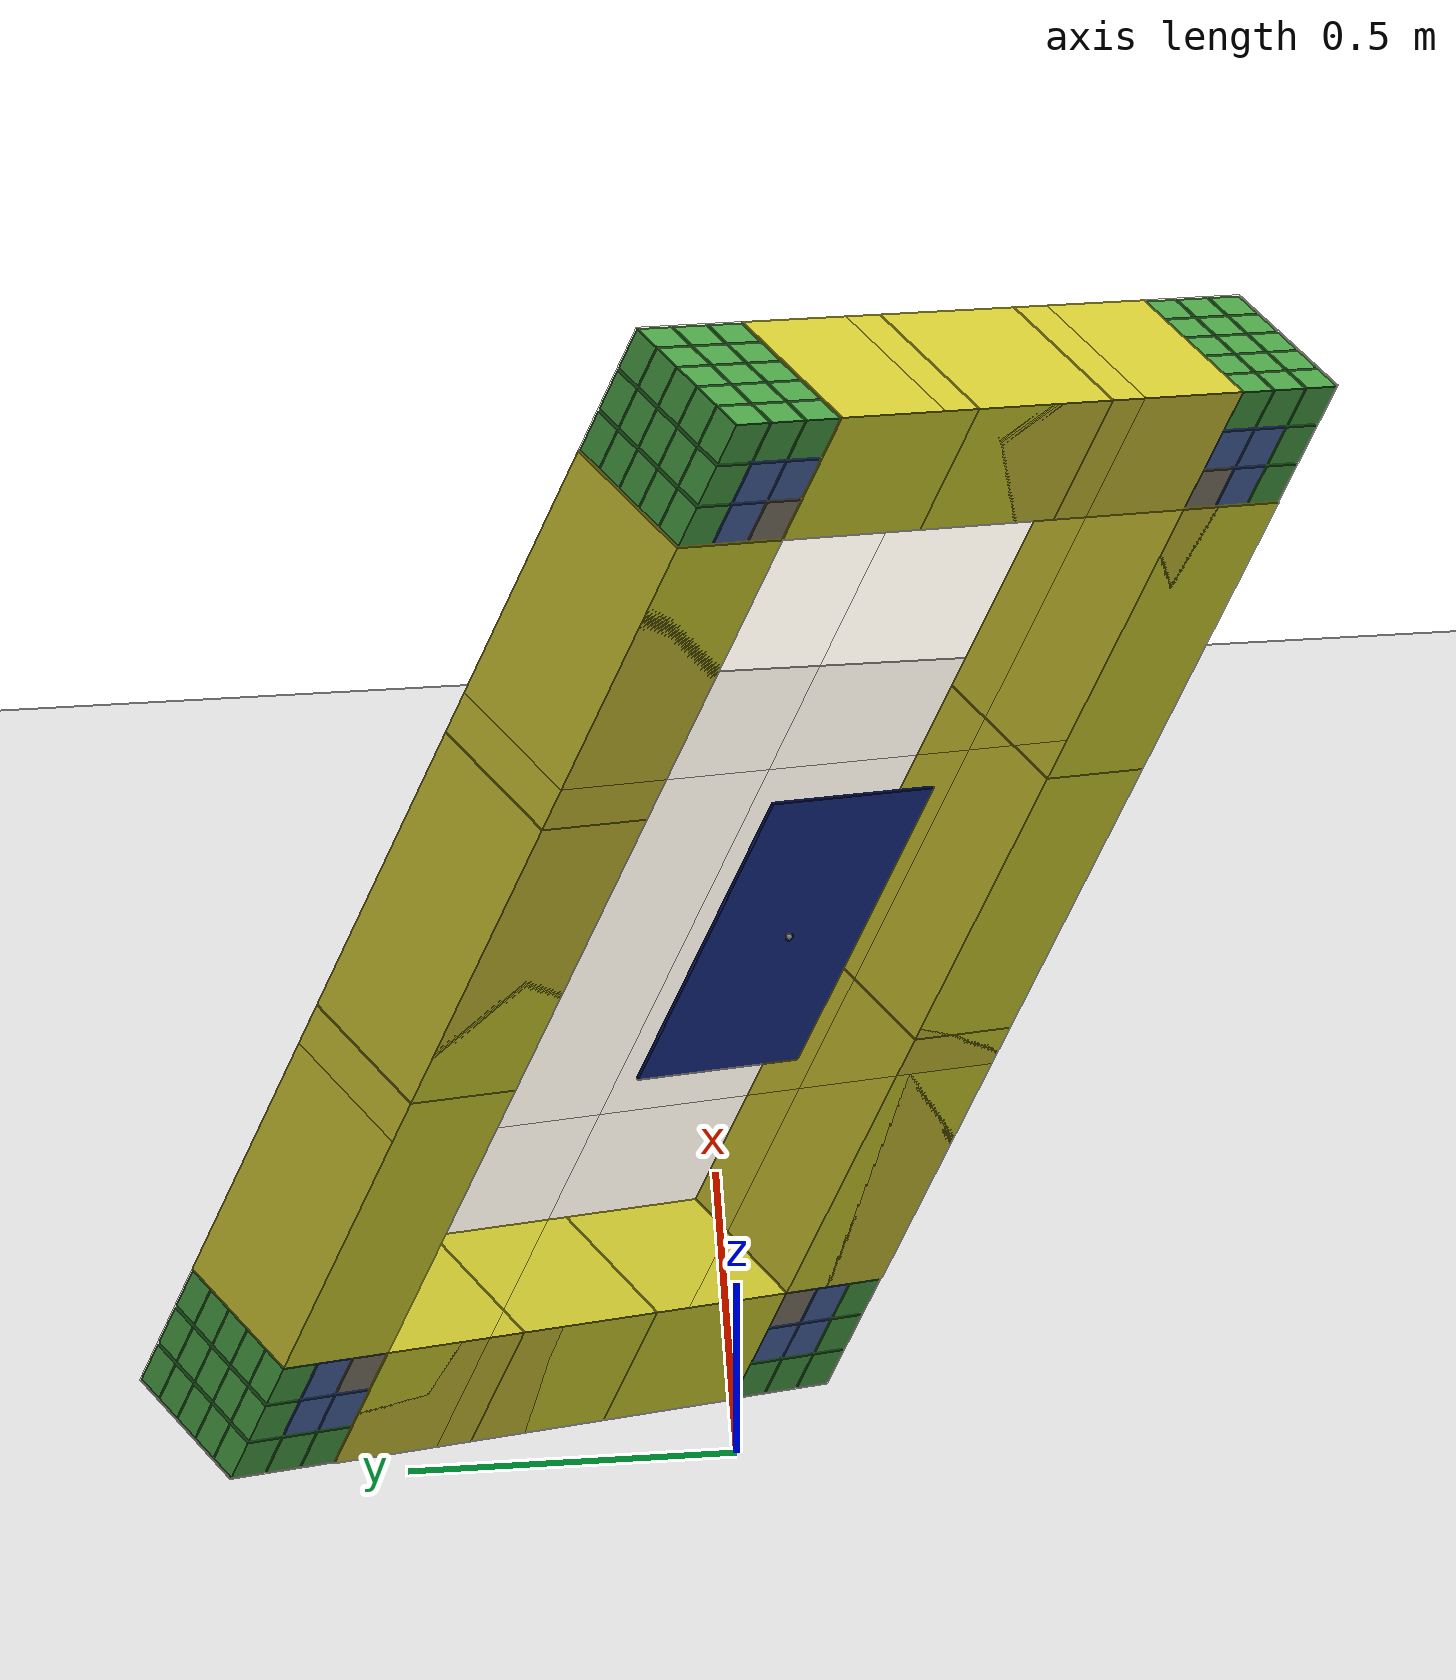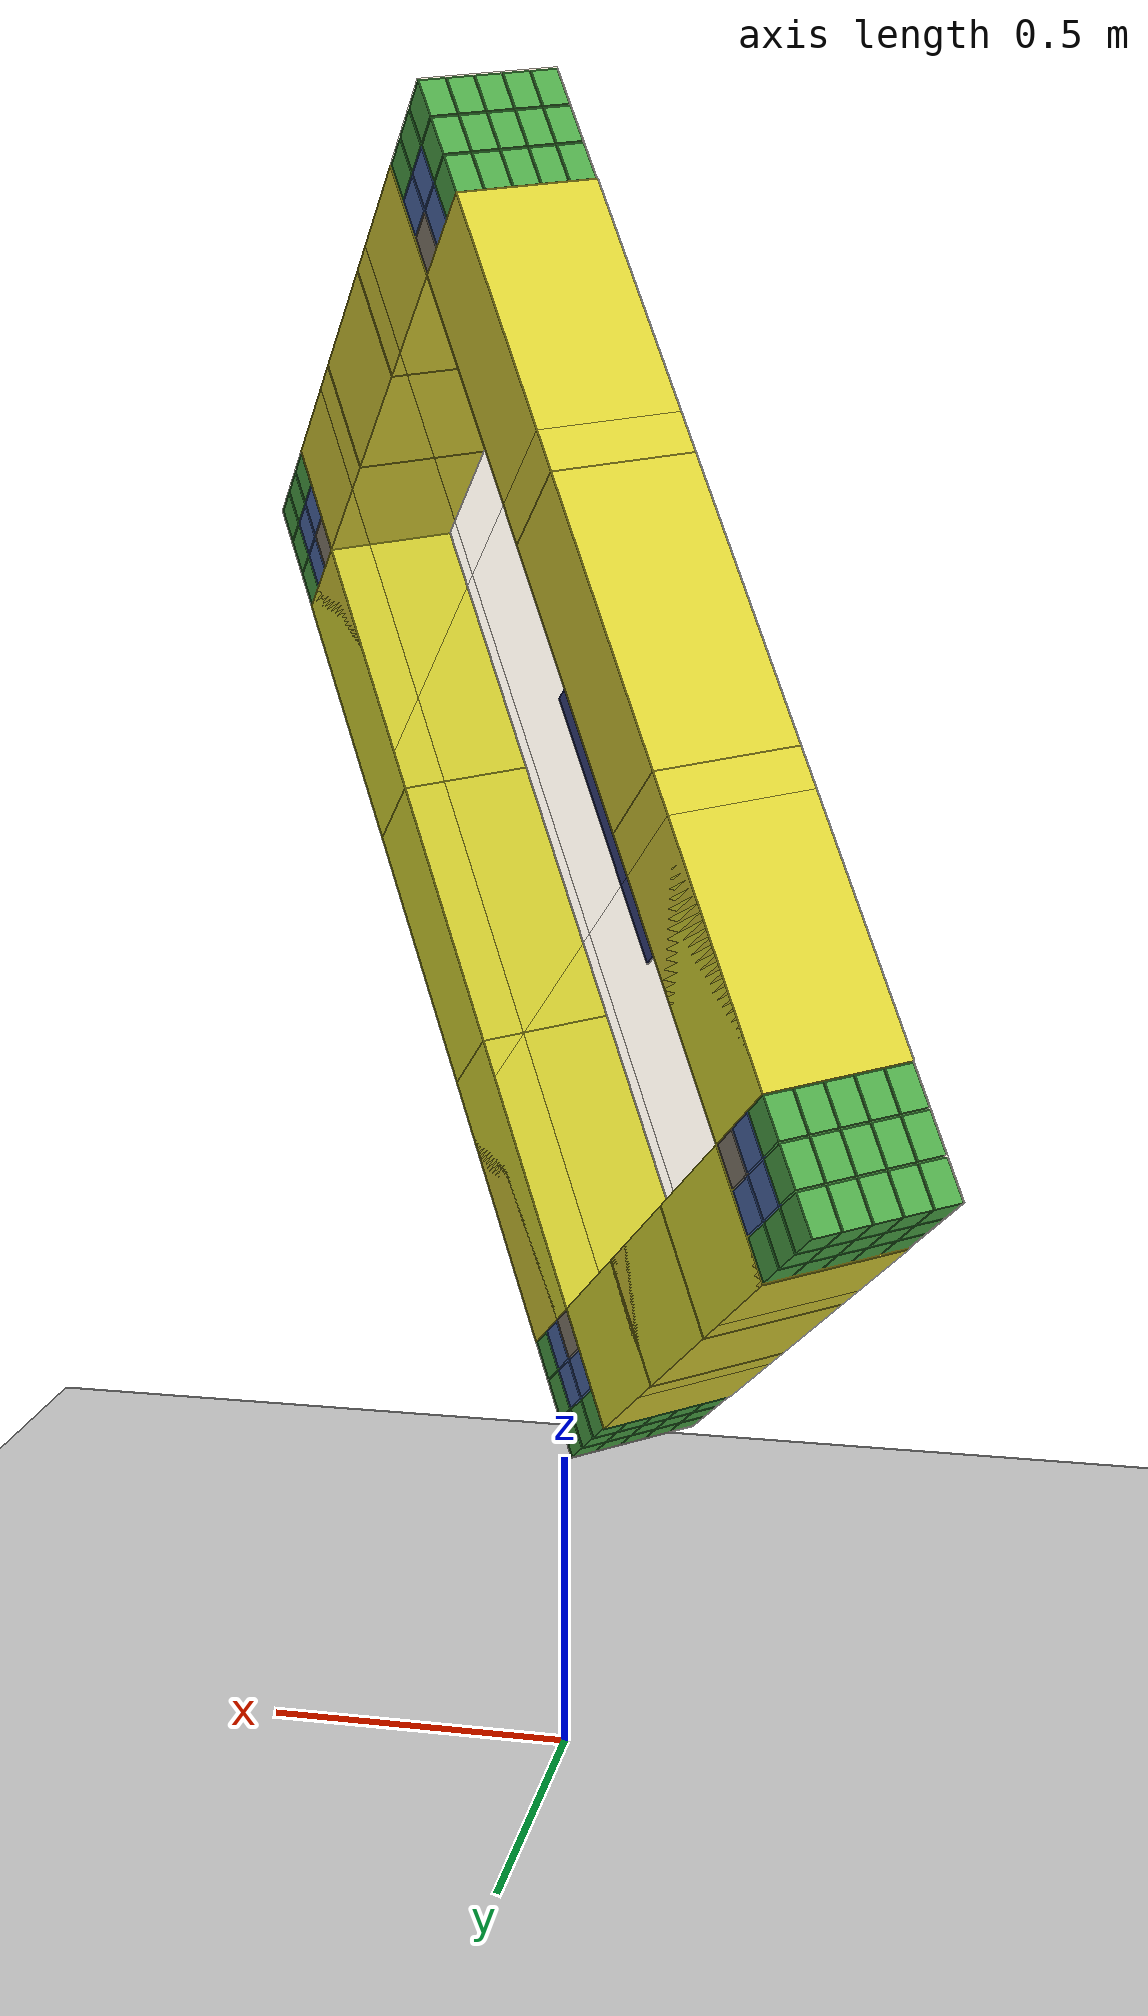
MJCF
<mujoco>
          <asset>
            <texture name="grid" type="2d" builtin="checker" rgb1=".8 .8 .8" rgb2=".9 .9 .9" width="300" height="300"/>
            <material name="grid" texture="grid" texrepeat="8 8" texuniform="true"/>
          </asset>

          <option timestep="0.001" gravity="0 0 -9.806" density="1.225" viscosity="1.8e-05"
                  iterations="30"
                  tolerance="0.0001"
                  solver="PGS"
                  cone="pyramidal">
            <flag contact="enable"/>
          </option>

          <worldbody>
            <light pos="10 10 20" dir="-1 -1 -1" diffuse="0.7 0.7 0.7"/>

        <geom name="floor_0" type="plane"
              pos="0 0 0" zaxis="0 0 1"
              size="1.4400000000000002 1.4400000000000002 1" material="grid"
              friction="0.3 0.005 0.0001" solref="0.01 1"
              contype="1" conaffinity="2"/>

                    <body name="box_0_c" pos="0 0 1.5871898646601788" quat="0.7447971394333582 0.3704541228168405 -0.5550020183334299 -0.003704541228168405">
                        <freejoint name="joint_0"/>
                        <inertial pos="0 0 0" mass="3.3333333333333335" diaginertia="0.41344444444444445 0.9134444444444445 1.2999999999999998"/>
<geom name="box_0_vis_c" type="box" size="0.3 0.19999999999999998 0.11" rgba="0.8 0.6 0.3 0.2" contype="0" conaffinity="0"/>
<geom name="box_0_brand" type="box" size="0.24 0.16 0.002" pos="0 0 0.111" rgba="0.1 0.2 0.6 1.0" mass="0.001"/>
<site name="box_0_label" pos="0 0 0.12" label="SAMSUNG"/>

                    <body name="box_0_sw" pos="-0.6 -0.39999999999999997 0">
                        <joint name="j_0_sw_x" type="hinge" axis="1 0 0" stiffness="8000.0" damping="200.0"/>
                        <joint name="j_0_sw_y" type="hinge" axis="0 1 0" stiffness="8000.0" damping="200.0"/>
                        <inertial pos="0 0 0" mass="3.3333333333333335" diaginertia="0.41344444444444445 0.9134444444444445 1.2999999999999998"/>
<geom name="box_0_vis_sw" type="box" size="0.3 0.19999999999999998 0.11" rgba="0.8 0.6 0.3 0.2" contype="0" conaffinity="0"/>

                    <geom name="box_0_v_corner_0_z0_x0_y0" type="box" size="0.031746031746031744 0.031746031746031744 0.02095238095238095"
                          pos="-0.13332333333333335 -0.033323333333333316 -0.088"
                          rgba="0.5 0.5 0.5 1.0" solref="0.05000 0.10000" solimp="0.2 0.7 0.02 0.5 2"
                          friction="0.3 0.005 0.0001" contype="2" conaffinity="3"/>

                    <geom name="box_0_v_corner_0_z0_x0_y1" type="box" size="0.031746031746031744 0.031746031746031744 0.02095238095238095"
                          pos="-0.13332333333333335 -0.09998999999999997 -0.088"
                          rgba="0.2 0.4 0.8 1.0" solref="0.05000 0.10000" solimp="0.2 0.7 0.02 0.5 2"
                          friction="0.3 0.005 0.0001" contype="2" conaffinity="3"/>

                    <geom name="box_0_v_corner_0_z0_x0_y2" type="box" size="0.031746031746031744 0.031746031746031744 0.02095238095238095"
                          pos="-0.13332333333333335 -0.16665666666666662 -0.088"
                          rgba="0.2 0.7 0.3 1.0" solref="0.05000 0.10000" solimp="0.2 0.7 0.02 0.5 2"
                          friction="0.3 0.005 0.0001" contype="2" conaffinity="3"/>

                    <geom name="box_0_v_corner_0_z0_x1_y0" type="box" size="0.031746031746031744 0.031746031746031744 0.02095238095238095"
                          pos="-0.19999 -0.033323333333333316 -0.088"
                          rgba="0.2 0.4 0.8 1.0" solref="0.05000 0.10000" solimp="0.2 0.7 0.02 0.5 2"
                          friction="0.3 0.005 0.0001" contype="2" conaffinity="3"/>

                    <geom name="box_0_v_corner_0_z0_x1_y1" type="box" size="0.031746031746031744 0.031746031746031744 0.02095238095238095"
                          pos="-0.19999 -0.09998999999999997 -0.088"
                          rgba="0.2 0.4 0.8 1.0" solref="0.05000 0.10000" solimp="0.2 0.7 0.02 0.5 2"
                          friction="0.3 0.005 0.0001" contype="2" conaffinity="3"/>

                    <geom name="box_0_v_corner_0_z0_x1_y2" type="box" size="0.031746031746031744 0.031746031746031744 0.02095238095238095"
                          pos="-0.19999 -0.16665666666666662 -0.088"
                          rgba="0.2 0.7 0.3 1.0" solref="0.05000 0.10000" solimp="0.2 0.7 0.02 0.5 2"
                          friction="0.3 0.005 0.0001" contype="2" conaffinity="3"/>

                    <geom name="box_0_v_corner_0_z0_x2_y0" type="box" size="0.031746031746031744 0.031746031746031744 0.02095238095238095"
                          pos="-0.26665666666666665 -0.033323333333333316 -0.088"
                          rgba="0.2 0.7 0.3 1.0" solref="0.05000 0.10000" solimp="0.2 0.7 0.02 0.5 2"
                          friction="0.3 0.005 0.0001" contype="2" conaffinity="3"/>

                    <geom name="box_0_v_corner_0_z0_x2_y1" type="box" size="0.031746031746031744 0.031746031746031744 0.02095238095238095"
                          pos="-0.26665666666666665 -0.09998999999999997 -0.088"
                          rgba="0.2 0.7 0.3 1.0" solref="0.05000 0.10000" solimp="0.2 0.7 0.02 0.5 2"
                          friction="0.3 0.005 0.0001" contype="2" conaffinity="3"/>

                    <geom name="box_0_v_corner_0_z0_x2_y2" type="box" size="0.031746031746031744 0.031746031746031744 0.02095238095238095"
                          pos="-0.26665666666666665 -0.16665666666666662 -0.088"
                          rgba="0.2 0.7 0.3 1.0" solref="0.05000 0.10000" solimp="0.2 0.7 0.02 0.5 2"
                          friction="0.3 0.005 0.0001" contype="2" conaffinity="3"/>

                    <geom name="box_0_v_corner_0_z1_x0_y0" type="box" size="0.031746031746031744 0.031746031746031744 0.02095238095238095"
                          pos="-0.13332333333333335 -0.033323333333333316 -0.044"
                          rgba="0.5 0.5 0.5 1.0" solref="0.05000 0.10000" solimp="0.2 0.7 0.02 0.5 2"
                          friction="0.3 0.005 0.0001" contype="2" conaffinity="3"/>

                    <geom name="box_0_v_corner_0_z1_x0_y1" type="box" size="0.031746031746031744 0.031746031746031744 0.02095238095238095"
                          pos="-0.13332333333333335 -0.09998999999999997 -0.044"
                          rgba="0.2 0.4 0.8 1.0" solref="0.05000 0.10000" solimp="0.2 0.7 0.02 0.5 2"
                          friction="0.3 0.005 0.0001" contype="2" conaffinity="3"/>

                    <geom name="box_0_v_corner_0_z1_x0_y2" type="box" size="0.031746031746031744 0.031746031746031744 0.02095238095238095"
                          pos="-0.13332333333333335 -0.16665666666666662 -0.044"
                          rgba="0.2 0.7 0.3 1.0" solref="0.05000 0.10000" solimp="0.2 0.7 0.02 0.5 2"
                          friction="0.3 0.005 0.0001" contype="2" conaffinity="3"/>

                    <geom name="box_0_v_corner_0_z1_x1_y0" type="box" size="0.031746031746031744 0.031746031746031744 0.02095238095238095"
                          pos="-0.19999 -0.033323333333333316 -0.044"
                          rgba="0.2 0.4 0.8 1.0" solref="0.05000 0.10000" solimp="0.2 0.7 0.02 0.5 2"
                          friction="0.3 0.005 0.0001" contype="2" conaffinity="3"/>

                    <geom name="box_0_v_corner_0_z1_x1_y1" type="box" size="0.031746031746031744 0.031746031746031744 0.02095238095238095"
                          pos="-0.19999 -0.09998999999999997 -0.044"
                          rgba="0.2 0.4 0.8 1.0" solref="0.05000 0.10000" solimp="0.2 0.7 0.02 0.5 2"
                          friction="0.3 0.005 0.0001" contype="2" conaffinity="3"/>

                    <geom name="box_0_v_corner_0_z1_x1_y2" type="box" size="0.031746031746031744 0.031746031746031744 0.02095238095238095"
                          pos="-0.19999 -0.16665666666666662 -0.044"
                          rgba="0.2 0.7 0.3 1.0" solref="0.05000 0.10000" solimp="0.2 0.7 0.02 0.5 2"
                          friction="0.3 0.005 0.0001" contype="2" conaffinity="3"/>

                    <geom name="box_0_v_corner_0_z1_x2_y0" type="box" size="0.031746031746031744 0.031746031746031744 0.02095238095238095"
                          pos="-0.26665666666666665 -0.033323333333333316 -0.044"
                          rgba="0.2 0.7 0.3 1.0" solref="0.05000 0.10000" solimp="0.2 0.7 0.02 0.5 2"
                          friction="0.3 0.005 0.0001" contype="2" conaffinity="3"/>

                    <geom name="box_0_v_corner_0_z1_x2_y1" type="box" size="0.031746031746031744 0.031746031746031744 0.02095238095238095"
                          pos="-0.26665666666666665 -0.09998999999999997 -0.044"
                          rgba="0.2 0.7 0.3 1.0" solref="0.05000 0.10000" solimp="0.2 0.7 0.02 0.5 2"
                          friction="0.3 0.005 0.0001" contype="2" conaffinity="3"/>

                    <geom name="box_0_v_corner_0_z1_x2_y2" type="box" size="0.031746031746031744 0.031746031746031744 0.02095238095238095"
                          pos="-0.26665666666666665 -0.16665666666666662 -0.044"
                          rgba="0.2 0.7 0.3 1.0" solref="0.05000 0.10000" solimp="0.2 0.7 0.02 0.5 2"
                          friction="0.3 0.005 0.0001" contype="2" conaffinity="3"/>

                    <geom name="box_0_v_corner_0_z2_x0_y0" type="box" size="0.031746031746031744 0.031746031746031744 0.02095238095238095"
                          pos="-0.13332333333333335 -0.033323333333333316 0.0"
                          rgba="0.5 0.5 0.5 1.0" solref="0.05000 0.10000" solimp="0.2 0.7 0.02 0.5 2"
                          friction="0.3 0.005 0.0001" contype="2" conaffinity="3"/>

                    <geom name="box_0_v_corner_0_z2_x0_y1" type="box" size="0.031746031746031744 0.031746031746031744 0.02095238095238095"
                          pos="-0.13332333333333335 -0.09998999999999997 0.0"
                          rgba="0.2 0.4 0.8 1.0" solref="0.05000 0.10000" solimp="0.2 0.7 0.02 0.5 2"
                          friction="0.3 0.005 0.0001" contype="2" conaffinity="3"/>

                    <geom name="box_0_v_corner_0_z2_x0_y2" type="box" size="0.031746031746031744 0.031746031746031744 0.02095238095238095"
                          pos="-0.13332333333333335 -0.16665666666666662 0.0"
                          rgba="0.2 0.7 0.3 1.0" solref="0.05000 0.10000" solimp="0.2 0.7 0.02 0.5 2"
                          friction="0.3 0.005 0.0001" contype="2" conaffinity="3"/>

                    <geom name="box_0_v_corner_0_z2_x1_y0" type="box" size="0.031746031746031744 0.031746031746031744 0.02095238095238095"
                          pos="-0.19999 -0.033323333333333316 0.0"
                          rgba="0.2 0.4 0.8 1.0" solref="0.05000 0.10000" solimp="0.2 0.7 0.02 0.5 2"
                          friction="0.3 0.005 0.0001" contype="2" conaffinity="3"/>

                    <geom name="box_0_v_corner_0_z2_x1_y1" type="box" size="0.031746031746031744 0.031746031746031744 0.02095238095238095"
                          pos="-0.19999 -0.09998999999999997 0.0"
                          rgba="0.2 0.4 0.8 1.0" solref="0.05000 0.10000" solimp="0.2 0.7 0.02 0.5 2"
                          friction="0.3 0.005 0.0001" contype="2" conaffinity="3"/>

                    <geom name="box_0_v_corner_0_z2_x1_y2" type="box" size="0.031746031746031744 0.031746031746031744 0.02095238095238095"
                          pos="-0.19999 -0.16665666666666662 0.0"
                          rgba="0.2 0.7 0.3 1.0" solref="0.05000 0.10000" solimp="0.2 0.7 0.02 0.5 2"
                          friction="0.3 0.005 0.0001" contype="2" conaffinity="3"/>

                    <geom name="box_0_v_corner_0_z2_x2_y0" type="box" size="0.031746031746031744 0.031746031746031744 0.02095238095238095"
                          pos="-0.26665666666666665 -0.033323333333333316 0.0"
                          rgba="0.2 0.7 0.3 1.0" solref="0.05000 0.10000" solimp="0.2 0.7 0.02 0.5 2"
                          friction="0.3 0.005 0.0001" contype="2" conaffinity="3"/>

                    <geom name="box_0_v_corner_0_z2_x2_y1" type="box" size="0.031746031746031744 0.031746031746031744 0.02095238095238095"
                          pos="-0.26665666666666665 -0.09998999999999997 0.0"
                          rgba="0.2 0.7 0.3 1.0" solref="0.05000 0.10000" solimp="0.2 0.7 0.02 0.5 2"
                          friction="0.3 0.005 0.0001" contype="2" conaffinity="3"/>

                    <geom name="box_0_v_corner_0_z2_x2_y2" type="box" size="0.031746031746031744 0.031746031746031744 0.02095238095238095"
                          pos="-0.26665666666666665 -0.16665666666666662 0.0"
                          rgba="0.2 0.7 0.3 1.0" solref="0.05000 0.10000" solimp="0.2 0.7 0.02 0.5 2"
                          friction="0.3 0.005 0.0001" contype="2" conaffinity="3"/>

                    <geom name="box_0_v_corner_0_z3_x0_y0" type="box" size="0.031746031746031744 0.031746031746031744 0.02095238095238095"
                          pos="-0.13332333333333335 -0.033323333333333316 0.044"
                          rgba="0.5 0.5 0.5 1.0" solref="0.05000 0.10000" solimp="0.2 0.7 0.02 0.5 2"
                          friction="0.3 0.005 0.0001" contype="2" conaffinity="3"/>

                    <geom name="box_0_v_corner_0_z3_x0_y1" type="box" size="0.031746031746031744 0.031746031746031744 0.02095238095238095"
                          pos="-0.13332333333333335 -0.09998999999999997 0.044"
                          rgba="0.2 0.4 0.8 1.0" solref="0.05000 0.10000" solimp="0.2 0.7 0.02 0.5 2"
                          friction="0.3 0.005 0.0001" contype="2" conaffinity="3"/>

                    <geom name="box_0_v_corner_0_z3_x0_y2" type="box" size="0.031746031746031744 0.031746031746031744 0.02095238095238095"
                          pos="-0.13332333333333335 -0.16665666666666662 0.044"
                          rgba="0.2 0.7 0.3 1.0" solref="0.05000 0.10000" solimp="0.2 0.7 0.02 0.5 2"
                          friction="0.3 0.005 0.0001" contype="2" conaffinity="3"/>

                    <geom name="box_0_v_corner_0_z3_x1_y0" type="box" size="0.031746031746031744 0.031746031746031744 0.02095238095238095"
                          pos="-0.19999 -0.033323333333333316 0.044"
                          rgba="0.2 0.4 0.8 1.0" solref="0.05000 0.10000" solimp="0.2 0.7 0.02 0.5 2"
                          friction="0.3 0.005 0.0001" contype="2" conaffinity="3"/>

                    <geom name="box_0_v_corner_0_z3_x1_y1" type="box" size="0.031746031746031744 0.031746031746031744 0.02095238095238095"
                          pos="-0.19999 -0.09998999999999997 0.044"
                          rgba="0.2 0.4 0.8 1.0" solref="0.05000 0.10000" solimp="0.2 0.7 0.02 0.5 2"
                          friction="0.3 0.005 0.0001" contype="2" conaffinity="3"/>

                    <geom name="box_0_v_corner_0_z3_x1_y2" type="box" size="0.031746031746031744 0.031746031746031744 0.02095238095238095"
                          pos="-0.19999 -0.16665666666666662 0.044"
                          rgba="0.2 0.7 0.3 1.0" solref="0.05000 0.10000" solimp="0.2 0.7 0.02 0.5 2"
                          friction="0.3 0.005 0.0001" contype="2" conaffinity="3"/>

                    <geom name="box_0_v_corner_0_z3_x2_y0" type="box" size="0.031746031746031744 0.031746031746031744 0.02095238095238095"
                          pos="-0.26665666666666665 -0.033323333333333316 0.044"
                          rgba="0.2 0.7 0.3 1.0" solref="0.05000 0.10000" solimp="0.2 0.7 0.02 0.5 2"
                          friction="0.3 0.005 0.0001" contype="2" conaffinity="3"/>

                    <geom name="box_0_v_corner_0_z3_x2_y1" type="box" size="0.031746031746031744 0.031746031746031744 0.02095238095238095"
                          pos="-0.26665666666666665 -0.09998999999999997 0.044"
                          rgba="0.2 0.7 0.3 1.0" solref="0.05000 0.10000" solimp="0.2 0.7 0.02 0.5 2"
                          friction="0.3 0.005 0.0001" contype="2" conaffinity="3"/>

                    <geom name="box_0_v_corner_0_z3_x2_y2" type="box" size="0.031746031746031744 0.031746031746031744 0.02095238095238095"
                          pos="-0.26665666666666665 -0.16665666666666662 0.044"
                          rgba="0.2 0.7 0.3 1.0" solref="0.05000 0.10000" solimp="0.2 0.7 0.02 0.5 2"
                          friction="0.3 0.005 0.0001" contype="2" conaffinity="3"/>

                    <geom name="box_0_v_corner_0_z4_x0_y0" type="box" size="0.031746031746031744 0.031746031746031744 0.02095238095238095"
                          pos="-0.13332333333333335 -0.033323333333333316 0.08800000000000001"
                          rgba="0.5 0.5 0.5 1.0" solref="0.05000 0.10000" solimp="0.2 0.7 0.02 0.5 2"
                          friction="0.3 0.005 0.0001" contype="2" conaffinity="3"/>

                    <geom name="box_0_v_corner_0_z4_x0_y1" type="box" size="0.031746031746031744 0.031746031746031744 0.02095238095238095"
                          pos="-0.13332333333333335 -0.09998999999999997 0.08800000000000001"
                          rgba="0.2 0.4 0.8 1.0" solref="0.05000 0.10000" solimp="0.2 0.7 0.02 0.5 2"
                          friction="0.3 0.005 0.0001" contype="2" conaffinity="3"/>

                    <geom name="box_0_v_corner_0_z4_x0_y2" type="box" size="0.031746031746031744 0.031746031746031744 0.02095238095238095"
                          pos="-0.13332333333333335 -0.16665666666666662 0.08800000000000001"
                          rgba="0.2 0.7 0.3 1.0" solref="0.05000 0.10000" solimp="0.2 0.7 0.02 0.5 2"
                          friction="0.3 0.005 0.0001" contype="2" conaffinity="3"/>

                    <geom name="box_0_v_corner_0_z4_x1_y0" type="box" size="0.031746031746031744 0.031746031746031744 0.02095238095238095"
                          pos="-0.19999 -0.033323333333333316 0.08800000000000001"
                          rgba="0.2 0.4 0.8 1.0" solref="0.05000 0.10000" solimp="0.2 0.7 0.02 0.5 2"
                          friction="0.3 0.005 0.0001" contype="2" conaffinity="3"/>

                    <geom name="box_0_v_corner_0_z4_x1_y1" type="box" size="0.031746031746031744 0.031746031746031744 0.02095238095238095"
                          pos="-0.19999 -0.09998999999999997 0.08800000000000001"
                          rgba="0.2 0.4 0.8 1.0" solref="0.05000 0.10000" solimp="0.2 0.7 0.02 0.5 2"
                          friction="0.3 0.005 0.0001" contype="2" conaffinity="3"/>

                    <geom name="box_0_v_corner_0_z4_x1_y2" type="box" size="0.031746031746031744 0.031746031746031744 0.02095238095238095"
                          pos="-0.19999 -0.16665666666666662 0.08800000000000001"
                          rgba="0.2 0.7 0.3 1.0" solref="0.05000 0.10000" solimp="0.2 0.7 0.02 0.5 2"
                          friction="0.3 0.005 0.0001" contype="2" conaffinity="3"/>

                    <geom name="box_0_v_corner_0_z4_x2_y0" type="box" size="0.031746031746031744 0.031746031746031744 0.02095238095238095"
                          pos="-0.26665666666666665 -0.033323333333333316 0.08800000000000001"
                          rgba="0.2 0.7 0.3 1.0" solref="0.05000 0.10000" solimp="0.2 0.7 0.02 0.5 2"
                          friction="0.3 0.005 0.0001" contype="2" conaffinity="3"/>

                    <geom name="box_0_v_corner_0_z4_x2_y1" type="box" size="0.031746031746031744 0.031746031746031744 0.02095238095238095"
                          pos="-0.26665666666666665 -0.09998999999999997 0.08800000000000001"
                          rgba="0.2 0.7 0.3 1.0" solref="0.05000 0.10000" solimp="0.2 0.7 0.02 0.5 2"
                          friction="0.3 0.005 0.0001" contype="2" conaffinity="3"/>

                    <geom name="box_0_v_corner_0_z4_x2_y2" type="box" size="0.031746031746031744 0.031746031746031744 0.02095238095238095"
                          pos="-0.26665666666666665 -0.16665666666666662 0.08800000000000001"
                          rgba="0.2 0.7 0.3 1.0" solref="0.05000 0.10000" solimp="0.2 0.7 0.02 0.5 2"
                          friction="0.3 0.005 0.0001" contype="2" conaffinity="3"/>

                    <geom name="box_0_h_edge_front_seg0" type="box" size="0.23333 0.1 0.11"
                          pos="0.13334000000000001 -0.09999000000000002 0"
                          rgba="0.9 0.9 0.2 1.0" solref="0.05000 0.10000" solimp="0.2 0.7 0.02 0.5 2"
                          friction="0.3 0.005 0.0001" contype="2" conaffinity="3"/>

                    <geom name="box_0_h_edge_left_seg0" type="box" size="0.1 0.13332999999999998 0.11"
                          pos="-0.1999900000000001 0.13333999999999996 0"
                          rgba="0.9 0.9 0.2 1.0" solref="0.05000 0.10000" solimp="0.2 0.7 0.02 0.5 2"
                          friction="0.3 0.005 0.0001" contype="2" conaffinity="3"/>

                    </body>
                    <body name="box_0_w" pos="-0.6 0.0 0">
                        <joint name="j_0_w_x" type="hinge" axis="1 0 0" stiffness="8000.0" damping="200.0"/>
                        <joint name="j_0_w_y" type="hinge" axis="0 1 0" stiffness="8000.0" damping="200.0"/>
                        <inertial pos="0 0 0" mass="3.3333333333333335" diaginertia="0.41344444444444445 0.9134444444444445 1.2999999999999998"/>
<geom name="box_0_vis_w" type="box" size="0.3 0.19999999999999998 0.11" rgba="0.8 0.6 0.3 0.2" contype="0" conaffinity="0"/>

                    <geom name="box_0_h_edge_left_seg1" type="box" size="0.1 0.13332999999999998 0.11"
                          pos="-0.1999900000000001 0.0 0"
                          rgba="0.9 0.9 0.2 1.0" solref="0.05000 0.10000" solimp="0.2 0.7 0.02 0.5 2"
                          friction="0.3 0.005 0.0001" contype="2" conaffinity="3"/>

                    </body>
                    <body name="box_0_nw" pos="-0.6 0.39999999999999997 0">
                        <joint name="j_0_nw_x" type="hinge" axis="1 0 0" stiffness="8000.0" damping="200.0"/>
                        <joint name="j_0_nw_y" type="hinge" axis="0 1 0" stiffness="8000.0" damping="200.0"/>
                        <inertial pos="0 0 0" mass="3.3333333333333335" diaginertia="0.41344444444444445 0.9134444444444445 1.2999999999999998"/>
<geom name="box_0_vis_nw" type="box" size="0.3 0.19999999999999998 0.11" rgba="0.8 0.6 0.3 0.2" contype="0" conaffinity="0"/>

                    <geom name="box_0_v_corner_1_z0_x0_y0" type="box" size="0.031746031746031744 0.031746031746031744 0.02095238095238095"
                          pos="-0.13332333333333335 0.033323333333333316 -0.088"
                          rgba="0.5 0.5 0.5 1.0" solref="0.05000 0.10000" solimp="0.2 0.7 0.02 0.5 2"
                          friction="0.3 0.005 0.0001" contype="2" conaffinity="3"/>

                    <geom name="box_0_v_corner_1_z0_x0_y1" type="box" size="0.031746031746031744 0.031746031746031744 0.02095238095238095"
                          pos="-0.13332333333333335 0.09998999999999997 -0.088"
                          rgba="0.2 0.4 0.8 1.0" solref="0.05000 0.10000" solimp="0.2 0.7 0.02 0.5 2"
                          friction="0.3 0.005 0.0001" contype="2" conaffinity="3"/>

                    <geom name="box_0_v_corner_1_z0_x0_y2" type="box" size="0.031746031746031744 0.031746031746031744 0.02095238095238095"
                          pos="-0.13332333333333335 0.16665666666666662 -0.088"
                          rgba="0.2 0.7 0.3 1.0" solref="0.05000 0.10000" solimp="0.2 0.7 0.02 0.5 2"
                          friction="0.3 0.005 0.0001" contype="2" conaffinity="3"/>

                    <geom name="box_0_v_corner_1_z0_x1_y0" type="box" size="0.031746031746031744 0.031746031746031744 0.02095238095238095"
                          pos="-0.19999 0.033323333333333316 -0.088"
                          rgba="0.2 0.4 0.8 1.0" solref="0.05000 0.10000" solimp="0.2 0.7 0.02 0.5 2"
                          friction="0.3 0.005 0.0001" contype="2" conaffinity="3"/>

                    <geom name="box_0_v_corner_1_z0_x1_y1" type="box" size="0.031746031746031744 0.031746031746031744 0.02095238095238095"
                          pos="-0.19999 0.09998999999999997 -0.088"
                          rgba="0.2 0.4 0.8 1.0" solref="0.05000 0.10000" solimp="0.2 0.7 0.02 0.5 2"
                          friction="0.3 0.005 0.0001" contype="2" conaffinity="3"/>

                    <geom name="box_0_v_corner_1_z0_x1_y2" type="box" size="0.031746031746031744 0.031746031746031744 0.02095238095238095"
                          pos="-0.19999 0.16665666666666662 -0.088"
                          rgba="0.2 0.7 0.3 1.0" solref="0.05000 0.10000" solimp="0.2 0.7 0.02 0.5 2"
                          friction="0.3 0.005 0.0001" contype="2" conaffinity="3"/>

                    <geom name="box_0_v_corner_1_z0_x2_y0" type="box" size="0.031746031746031744 0.031746031746031744 0.02095238095238095"
                          pos="-0.26665666666666665 0.033323333333333316 -0.088"
                          rgba="0.2 0.7 0.3 1.0" solref="0.05000 0.10000" solimp="0.2 0.7 0.02 0.5 2"
                          friction="0.3 0.005 0.0001" contype="2" conaffinity="3"/>

                    <geom name="box_0_v_corner_1_z0_x2_y1" type="box" size="0.031746031746031744 0.031746031746031744 0.02095238095238095"
                          pos="-0.26665666666666665 0.09998999999999997 -0.088"
                          rgba="0.2 0.7 0.3 1.0" solref="0.05000 0.10000" solimp="0.2 0.7 0.02 0.5 2"
                          friction="0.3 0.005 0.0001" contype="2" conaffinity="3"/>

                    <geom name="box_0_v_corner_1_z0_x2_y2" type="box" size="0.031746031746031744 0.031746031746031744 0.02095238095238095"
                          pos="-0.26665666666666665 0.16665666666666662 -0.088"
                          rgba="0.2 0.7 0.3 1.0" solref="0.05000 0.10000" solimp="0.2 0.7 0.02 0.5 2"
                          friction="0.3 0.005 0.0001" contype="2" conaffinity="3"/>

                    <geom name="box_0_v_corner_1_z1_x0_y0" type="box" size="0.031746031746031744 0.031746031746031744 0.02095238095238095"
                          pos="-0.13332333333333335 0.033323333333333316 -0.044"
                          rgba="0.5 0.5 0.5 1.0" solref="0.05000 0.10000" solimp="0.2 0.7 0.02 0.5 2"
                          friction="0.3 0.005 0.0001" contype="2" conaffinity="3"/>

                    <geom name="box_0_v_corner_1_z1_x0_y1" type="box" size="0.031746031746031744 0.031746031746031744 0.02095238095238095"
                          pos="-0.13332333333333335 0.09998999999999997 -0.044"
                          rgba="0.2 0.4 0.8 1.0" solref="0.05000 0.10000" solimp="0.2 0.7 0.02 0.5 2"
                          friction="0.3 0.005 0.0001" contype="2" conaffinity="3"/>

                    <geom name="box_0_v_corner_1_z1_x0_y2" type="box" size="0.031746031746031744 0.031746031746031744 0.02095238095238095"
                          pos="-0.13332333333333335 0.16665666666666662 -0.044"
                          rgba="0.2 0.7 0.3 1.0" solref="0.05000 0.10000" solimp="0.2 0.7 0.02 0.5 2"
                          friction="0.3 0.005 0.0001" contype="2" conaffinity="3"/>

                    <geom name="box_0_v_corner_1_z1_x1_y0" type="box" size="0.031746031746031744 0.031746031746031744 0.02095238095238095"
                          pos="-0.19999 0.033323333333333316 -0.044"
                          rgba="0.2 0.4 0.8 1.0" solref="0.05000 0.10000" solimp="0.2 0.7 0.02 0.5 2"
                          friction="0.3 0.005 0.0001" contype="2" conaffinity="3"/>

                    <geom name="box_0_v_corner_1_z1_x1_y1" type="box" size="0.031746031746031744 0.031746031746031744 0.02095238095238095"
                          pos="-0.19999 0.09998999999999997 -0.044"
                          rgba="0.2 0.4 0.8 1.0" solref="0.05000 0.10000" solimp="0.2 0.7 0.02 0.5 2"
                          friction="0.3 0.005 0.0001" contype="2" conaffinity="3"/>

                    <geom name="box_0_v_corner_1_z1_x1_y2" type="box" size="0.031746031746031744 0.031746031746031744 0.02095238095238095"
                          pos="-0.19999 0.16665666666666662 -0.044"
                          rgba="0.2 0.7 0.3 1.0" solref="0.05000 0.10000" solimp="0.2 0.7 0.02 0.5 2"
                          friction="0.3 0.005 0.0001" contype="2" conaffinity="3"/>

                    <geom name="box_0_v_corner_1_z1_x2_y0" type="box" size="0.031746031746031744 0.031746031746031744 0.02095238095238095"
                          pos="-0.26665666666666665 0.033323333333333316 -0.044"
                          rgba="0.2 0.7 0.3 1.0" solref="0.05000 0.10000" solimp="0.2 0.7 0.02 0.5 2"
                          friction="0.3 0.005 0.0001" contype="2" conaffinity="3"/>

                    <geom name="box_0_v_corner_1_z1_x2_y1" type="box" size="0.031746031746031744 0.031746031746031744 0.02095238095238095"
                          pos="-0.26665666666666665 0.09998999999999997 -0.044"
                          rgba="0.2 0.7 0.3 1.0" solref="0.05000 0.10000" solimp="0.2 0.7 0.02 0.5 2"
                          friction="0.3 0.005 0.0001" contype="2" conaffinity="3"/>

                    <geom name="box_0_v_corner_1_z1_x2_y2" type="box" size="0.031746031746031744 0.031746031746031744 0.02095238095238095"
                          pos="-0.26665666666666665 0.16665666666666662 -0.044"
                          rgba="0.2 0.7 0.3 1.0" solref="0.05000 0.10000" solimp="0.2 0.7 0.02 0.5 2"
                          friction="0.3 0.005 0.0001" contype="2" conaffinity="3"/>

                    <geom name="box_0_v_corner_1_z2_x0_y0" type="box" size="0.031746031746031744 0.031746031746031744 0.02095238095238095"
                          pos="-0.13332333333333335 0.033323333333333316 0.0"
                          rgba="0.5 0.5 0.5 1.0" solref="0.05000 0.10000" solimp="0.2 0.7 0.02 0.5 2"
                          friction="0.3 0.005 0.0001" contype="2" conaffinity="3"/>

                    <geom name="box_0_v_corner_1_z2_x0_y1" type="box" size="0.031746031746031744 0.031746031746031744 0.02095238095238095"
                          pos="-0.13332333333333335 0.09998999999999997 0.0"
                          rgba="0.2 0.4 0.8 1.0" solref="0.05000 0.10000" solimp="0.2 0.7 0.02 0.5 2"
                          friction="0.3 0.005 0.0001" contype="2" conaffinity="3"/>

                    <geom name="box_0_v_corner_1_z2_x0_y2" type="box" size="0.031746031746031744 0.031746031746031744 0.02095238095238095"
                          pos="-0.13332333333333335 0.16665666666666662 0.0"
                          rgba="0.2 0.7 0.3 1.0" solref="0.05000 0.10000" solimp="0.2 0.7 0.02 0.5 2"
                          friction="0.3 0.005 0.0001" contype="2" conaffinity="3"/>

                    <geom name="box_0_v_corner_1_z2_x1_y0" type="box" size="0.031746031746031744 0.031746031746031744 0.02095238095238095"
                          pos="-0.19999 0.033323333333333316 0.0"
                          rgba="0.2 0.4 0.8 1.0" solref="0.05000 0.10000" solimp="0.2 0.7 0.02 0.5 2"
                          friction="0.3 0.005 0.0001" contype="2" conaffinity="3"/>

                    <geom name="box_0_v_corner_1_z2_x1_y1" type="box" size="0.031746031746031744 0.031746031746031744 0.02095238095238095"
                          pos="-0.19999 0.09998999999999997 0.0"
                          rgba="0.2 0.4 0.8 1.0" solref="0.05000 0.10000" solimp="0.2 0.7 0.02 0.5 2"
                          friction="0.3 0.005 0.0001" contype="2" conaffinity="3"/>

                    <geom name="box_0_v_corner_1_z2_x1_y2" type="box" size="0.031746031746031744 0.031746031746031744 0.02095238095238095"
                          pos="-0.19999 0.16665666666666662 0.0"
                          rgba="0.2 0.7 0.3 1.0" solref="0.05000 0.10000" solimp="0.2 0.7 0.02 0.5 2"
                          friction="0.3 0.005 0.0001" contype="2" conaffinity="3"/>

                    <geom name="box_0_v_corner_1_z2_x2_y0" type="box" size="0.031746031746031744 0.031746031746031744 0.02095238095238095"
                          pos="-0.26665666666666665 0.033323333333333316 0.0"
                          rgba="0.2 0.7 0.3 1.0" solref="0.05000 0.10000" solimp="0.2 0.7 0.02 0.5 2"
                          friction="0.3 0.005 0.0001" contype="2" conaffinity="3"/>

                    <geom name="box_0_v_corner_1_z2_x2_y1" type="box" size="0.031746031746031744 0.031746031746031744 0.02095238095238095"
                          pos="-0.26665666666666665 0.09998999999999997 0.0"
                          rgba="0.2 0.7 0.3 1.0" solref="0.05000 0.10000" solimp="0.2 0.7 0.02 0.5 2"
                          friction="0.3 0.005 0.0001" contype="2" conaffinity="3"/>

                    <geom name="box_0_v_corner_1_z2_x2_y2" type="box" size="0.031746031746031744 0.031746031746031744 0.02095238095238095"
                          pos="-0.26665666666666665 0.16665666666666662 0.0"
                          rgba="0.2 0.7 0.3 1.0" solref="0.05000 0.10000" solimp="0.2 0.7 0.02 0.5 2"
                          friction="0.3 0.005 0.0001" contype="2" conaffinity="3"/>

                    <geom name="box_0_v_corner_1_z3_x0_y0" type="box" size="0.031746031746031744 0.031746031746031744 0.02095238095238095"
                          pos="-0.13332333333333335 0.033323333333333316 0.044"
                          rgba="0.5 0.5 0.5 1.0" solref="0.05000 0.10000" solimp="0.2 0.7 0.02 0.5 2"
                          friction="0.3 0.005 0.0001" contype="2" conaffinity="3"/>

                    <geom name="box_0_v_corner_1_z3_x0_y1" type="box" size="0.031746031746031744 0.031746031746031744 0.02095238095238095"
                          pos="-0.13332333333333335 0.09998999999999997 0.044"
                          rgba="0.2 0.4 0.8 1.0" solref="0.05000 0.10000" solimp="0.2 0.7 0.02 0.5 2"
                          friction="0.3 0.005 0.0001" contype="2" conaffinity="3"/>

                    <geom name="box_0_v_corner_1_z3_x0_y2" type="box" size="0.031746031746031744 0.031746031746031744 0.02095238095238095"
                          pos="-0.13332333333333335 0.16665666666666662 0.044"
                          rgba="0.2 0.7 0.3 1.0" solref="0.05000 0.10000" solimp="0.2 0.7 0.02 0.5 2"
                          friction="0.3 0.005 0.0001" contype="2" conaffinity="3"/>

                    <geom name="box_0_v_corner_1_z3_x1_y0" type="box" size="0.031746031746031744 0.031746031746031744 0.02095238095238095"
                          pos="-0.19999 0.033323333333333316 0.044"
                          rgba="0.2 0.4 0.8 1.0" solref="0.05000 0.10000" solimp="0.2 0.7 0.02 0.5 2"
                          friction="0.3 0.005 0.0001" contype="2" conaffinity="3"/>

                    <geom name="box_0_v_corner_1_z3_x1_y1" type="box" size="0.031746031746031744 0.031746031746031744 0.02095238095238095"
                          pos="-0.19999 0.09998999999999997 0.044"
                          rgba="0.2 0.4 0.8 1.0" solref="0.05000 0.10000" solimp="0.2 0.7 0.02 0.5 2"
                          friction="0.3 0.005 0.0001" contype="2" conaffinity="3"/>

                    <geom name="box_0_v_corner_1_z3_x1_y2" type="box" size="0.031746031746031744 0.031746031746031744 0.02095238095238095"
                          pos="-0.19999 0.16665666666666662 0.044"
                          rgba="0.2 0.7 0.3 1.0" solref="0.05000 0.10000" solimp="0.2 0.7 0.02 0.5 2"
                          friction="0.3 0.005 0.0001" contype="2" conaffinity="3"/>

                    <geom name="box_0_v_corner_1_z3_x2_y0" type="box" size="0.031746031746031744 0.031746031746031744 0.02095238095238095"
                          pos="-0.26665666666666665 0.033323333333333316 0.044"
                          rgba="0.2 0.7 0.3 1.0" solref="0.05000 0.10000" solimp="0.2 0.7 0.02 0.5 2"
                          friction="0.3 0.005 0.0001" contype="2" conaffinity="3"/>

                    <geom name="box_0_v_corner_1_z3_x2_y1" type="box" size="0.031746031746031744 0.031746031746031744 0.02095238095238095"
                          pos="-0.26665666666666665 0.09998999999999997 0.044"
                          rgba="0.2 0.7 0.3 1.0" solref="0.05000 0.10000" solimp="0.2 0.7 0.02 0.5 2"
                          friction="0.3 0.005 0.0001" contype="2" conaffinity="3"/>

                    <geom name="box_0_v_corner_1_z3_x2_y2" type="box" size="0.031746031746031744 0.031746031746031744 0.02095238095238095"
                          pos="-0.26665666666666665 0.16665666666666662 0.044"
                          rgba="0.2 0.7 0.3 1.0" solref="0.05000 0.10000" solimp="0.2 0.7 0.02 0.5 2"
                          friction="0.3 0.005 0.0001" contype="2" conaffinity="3"/>

                    <geom name="box_0_v_corner_1_z4_x0_y0" type="box" size="0.031746031746031744 0.031746031746031744 0.02095238095238095"
                          pos="-0.13332333333333335 0.033323333333333316 0.08800000000000001"
                          rgba="0.5 0.5 0.5 1.0" solref="0.05000 0.10000" solimp="0.2 0.7 0.02 0.5 2"
                          friction="0.3 0.005 0.0001" contype="2" conaffinity="3"/>

                    <geom name="box_0_v_corner_1_z4_x0_y1" type="box" size="0.031746031746031744 0.031746031746031744 0.02095238095238095"
                          pos="-0.13332333333333335 0.09998999999999997 0.08800000000000001"
                          rgba="0.2 0.4 0.8 1.0" solref="0.05000 0.10000" solimp="0.2 0.7 0.02 0.5 2"
                          friction="0.3 0.005 0.0001" contype="2" conaffinity="3"/>

                    <geom name="box_0_v_corner_1_z4_x0_y2" type="box" size="0.031746031746031744 0.031746031746031744 0.02095238095238095"
                          pos="-0.13332333333333335 0.16665666666666662 0.08800000000000001"
                          rgba="0.2 0.7 0.3 1.0" solref="0.05000 0.10000" solimp="0.2 0.7 0.02 0.5 2"
                          friction="0.3 0.005 0.0001" contype="2" conaffinity="3"/>

                    <geom name="box_0_v_corner_1_z4_x1_y0" type="box" size="0.031746031746031744 0.031746031746031744 0.02095238095238095"
                          pos="-0.19999 0.033323333333333316 0.08800000000000001"
                          rgba="0.2 0.4 0.8 1.0" solref="0.05000 0.10000" solimp="0.2 0.7 0.02 0.5 2"
                          friction="0.3 0.005 0.0001" contype="2" conaffinity="3"/>

                    <geom name="box_0_v_corner_1_z4_x1_y1" type="box" size="0.031746031746031744 0.031746031746031744 0.02095238095238095"
                          pos="-0.19999 0.09998999999999997 0.08800000000000001"
                          rgba="0.2 0.4 0.8 1.0" solref="0.05000 0.10000" solimp="0.2 0.7 0.02 0.5 2"
                          friction="0.3 0.005 0.0001" contype="2" conaffinity="3"/>

                    <geom name="box_0_v_corner_1_z4_x1_y2" type="box" size="0.031746031746031744 0.031746031746031744 0.02095238095238095"
                          pos="-0.19999 0.16665666666666662 0.08800000000000001"
                          rgba="0.2 0.7 0.3 1.0" solref="0.05000 0.10000" solimp="0.2 0.7 0.02 0.5 2"
                          friction="0.3 0.005 0.0001" contype="2" conaffinity="3"/>

                    <geom name="box_0_v_corner_1_z4_x2_y0" type="box" size="0.031746031746031744 0.031746031746031744 0.02095238095238095"
                          pos="-0.26665666666666665 0.033323333333333316 0.08800000000000001"
                          rgba="0.2 0.7 0.3 1.0" solref="0.05000 0.10000" solimp="0.2 0.7 0.02 0.5 2"
                          friction="0.3 0.005 0.0001" contype="2" conaffinity="3"/>

                    <geom name="box_0_v_corner_1_z4_x2_y1" type="box" size="0.031746031746031744 0.031746031746031744 0.02095238095238095"
                          pos="-0.26665666666666665 0.09998999999999997 0.08800000000000001"
                          rgba="0.2 0.7 0.3 1.0" solref="0.05000 0.10000" solimp="0.2 0.7 0.02 0.5 2"
                          friction="0.3 0.005 0.0001" contype="2" conaffinity="3"/>

                    <geom name="box_0_v_corner_1_z4_x2_y2" type="box" size="0.031746031746031744 0.031746031746031744 0.02095238095238095"
                          pos="-0.26665666666666665 0.16665666666666662 0.08800000000000001"
                          rgba="0.2 0.7 0.3 1.0" solref="0.05000 0.10000" solimp="0.2 0.7 0.02 0.5 2"
                          friction="0.3 0.005 0.0001" contype="2" conaffinity="3"/>

                    <geom name="box_0_h_edge_back_seg0" type="box" size="0.23333 0.1 0.11"
                          pos="0.13334000000000001 0.09999000000000002 0"
                          rgba="0.9 0.9 0.2 1.0" solref="0.05000 0.10000" solimp="0.2 0.7 0.02 0.5 2"
                          friction="0.3 0.005 0.0001" contype="2" conaffinity="3"/>

                    <geom name="box_0_h_edge_left_seg2" type="box" size="0.1 0.13332999999999998 0.11"
                          pos="-0.1999900000000001 -0.13334000000000007 0"
                          rgba="0.9 0.9 0.2 1.0" solref="0.05000 0.10000" solimp="0.2 0.7 0.02 0.5 2"
                          friction="0.3 0.005 0.0001" contype="2" conaffinity="3"/>

                    </body>
                    <body name="box_0_s" pos="0.0 -0.39999999999999997 0">
                        <joint name="j_0_s_x" type="hinge" axis="1 0 0" stiffness="8000.0" damping="200.0"/>
                        <joint name="j_0_s_y" type="hinge" axis="0 1 0" stiffness="8000.0" damping="200.0"/>
                        <inertial pos="0 0 0" mass="3.3333333333333335" diaginertia="0.41344444444444445 0.9134444444444445 1.2999999999999998"/>
<geom name="box_0_vis_s" type="box" size="0.3 0.19999999999999998 0.11" rgba="0.8 0.6 0.3 0.2" contype="0" conaffinity="0"/>

                    <geom name="box_0_h_edge_front_seg1" type="box" size="0.23333 0.1 0.11"
                          pos="0.0 -0.09999000000000002 0"
                          rgba="0.9 0.9 0.2 1.0" solref="0.05000 0.10000" solimp="0.2 0.7 0.02 0.5 2"
                          friction="0.3 0.005 0.0001" contype="2" conaffinity="3"/>

                    </body>
                    <body name="box_0_n" pos="0.0 0.39999999999999997 0">
                        <joint name="j_0_n_x" type="hinge" axis="1 0 0" stiffness="8000.0" damping="200.0"/>
                        <joint name="j_0_n_y" type="hinge" axis="0 1 0" stiffness="8000.0" damping="200.0"/>
                        <inertial pos="0 0 0" mass="3.3333333333333335" diaginertia="0.41344444444444445 0.9134444444444445 1.2999999999999998"/>
<geom name="box_0_vis_n" type="box" size="0.3 0.19999999999999998 0.11" rgba="0.8 0.6 0.3 0.2" contype="0" conaffinity="0"/>

                    <geom name="box_0_h_edge_back_seg1" type="box" size="0.23333 0.1 0.11"
                          pos="0.0 0.09999000000000002 0"
                          rgba="0.9 0.9 0.2 1.0" solref="0.05000 0.10000" solimp="0.2 0.7 0.02 0.5 2"
                          friction="0.3 0.005 0.0001" contype="2" conaffinity="3"/>

                    </body>
                    <body name="box_0_se" pos="0.6 -0.39999999999999997 0">
                        <joint name="j_0_se_x" type="hinge" axis="1 0 0" stiffness="8000.0" damping="200.0"/>
                        <joint name="j_0_se_y" type="hinge" axis="0 1 0" stiffness="8000.0" damping="200.0"/>
                        <inertial pos="0 0 0" mass="3.3333333333333335" diaginertia="0.41344444444444445 0.9134444444444445 1.2999999999999998"/>
<geom name="box_0_vis_se" type="box" size="0.3 0.19999999999999998 0.11" rgba="0.8 0.6 0.3 0.2" contype="0" conaffinity="0"/>

                    <geom name="box_0_v_corner_2_z0_x0_y0" type="box" size="0.031746031746031744 0.031746031746031744 0.02095238095238095"
                          pos="0.13332333333333335 -0.033323333333333316 -0.088"
                          rgba="0.5 0.5 0.5 1.0" solref="0.05000 0.10000" solimp="0.2 0.7 0.02 0.5 2"
                          friction="0.3 0.005 0.0001" contype="2" conaffinity="3"/>

                    <geom name="box_0_v_corner_2_z0_x0_y1" type="box" size="0.031746031746031744 0.031746031746031744 0.02095238095238095"
                          pos="0.13332333333333335 -0.09998999999999997 -0.088"
                          rgba="0.2 0.4 0.8 1.0" solref="0.05000 0.10000" solimp="0.2 0.7 0.02 0.5 2"
                          friction="0.3 0.005 0.0001" contype="2" conaffinity="3"/>

                    <geom name="box_0_v_corner_2_z0_x0_y2" type="box" size="0.031746031746031744 0.031746031746031744 0.02095238095238095"
                          pos="0.13332333333333335 -0.16665666666666662 -0.088"
                          rgba="0.2 0.7 0.3 1.0" solref="0.05000 0.10000" solimp="0.2 0.7 0.02 0.5 2"
                          friction="0.3 0.005 0.0001" contype="2" conaffinity="3"/>

                    <geom name="box_0_v_corner_2_z0_x1_y0" type="box" size="0.031746031746031744 0.031746031746031744 0.02095238095238095"
                          pos="0.19999 -0.033323333333333316 -0.088"
                          rgba="0.2 0.4 0.8 1.0" solref="0.05000 0.10000" solimp="0.2 0.7 0.02 0.5 2"
                          friction="0.3 0.005 0.0001" contype="2" conaffinity="3"/>

                    <geom name="box_0_v_corner_2_z0_x1_y1" type="box" size="0.031746031746031744 0.031746031746031744 0.02095238095238095"
                          pos="0.19999 -0.09998999999999997 -0.088"
                          rgba="0.2 0.4 0.8 1.0" solref="0.05000 0.10000" solimp="0.2 0.7 0.02 0.5 2"
                          friction="0.3 0.005 0.0001" contype="2" conaffinity="3"/>

                    <geom name="box_0_v_corner_2_z0_x1_y2" type="box" size="0.031746031746031744 0.031746031746031744 0.02095238095238095"
                          pos="0.19999 -0.16665666666666662 -0.088"
                          rgba="0.2 0.7 0.3 1.0" solref="0.05000 0.10000" solimp="0.2 0.7 0.02 0.5 2"
                          friction="0.3 0.005 0.0001" contype="2" conaffinity="3"/>

                    <geom name="box_0_v_corner_2_z0_x2_y0" type="box" size="0.031746031746031744 0.031746031746031744 0.02095238095238095"
                          pos="0.26665666666666665 -0.033323333333333316 -0.088"
                          rgba="0.2 0.7 0.3 1.0" solref="0.05000 0.10000" solimp="0.2 0.7 0.02 0.5 2"
                          friction="0.3 0.005 0.0001" contype="2" conaffinity="3"/>

                    <geom name="box_0_v_corner_2_z0_x2_y1" type="box" size="0.031746031746031744 0.031746031746031744 0.02095238095238095"
                          pos="0.26665666666666665 -0.09998999999999997 -0.088"
                          rgba="0.2 0.7 0.3 1.0" solref="0.05000 0.10000" solimp="0.2 0.7 0.02 0.5 2"
                          friction="0.3 0.005 0.0001" contype="2" conaffinity="3"/>

                    <geom name="box_0_v_corner_2_z0_x2_y2" type="box" size="0.031746031746031744 0.031746031746031744 0.02095238095238095"
                          pos="0.26665666666666665 -0.16665666666666662 -0.088"
                          rgba="0.2 0.7 0.3 1.0" solref="0.05000 0.10000" solimp="0.2 0.7 0.02 0.5 2"
                          friction="0.3 0.005 0.0001" contype="2" conaffinity="3"/>

                    <geom name="box_0_v_corner_2_z1_x0_y0" type="box" size="0.031746031746031744 0.031746031746031744 0.02095238095238095"
                          pos="0.13332333333333335 -0.033323333333333316 -0.044"
                          rgba="0.5 0.5 0.5 1.0" solref="0.05000 0.10000" solimp="0.2 0.7 0.02 0.5 2"
                          friction="0.3 0.005 0.0001" contype="2" conaffinity="3"/>

                    <geom name="box_0_v_corner_2_z1_x0_y1" type="box" size="0.031746031746031744 0.031746031746031744 0.02095238095238095"
                          pos="0.13332333333333335 -0.09998999999999997 -0.044"
                          rgba="0.2 0.4 0.8 1.0" solref="0.05000 0.10000" solimp="0.2 0.7 0.02 0.5 2"
                          friction="0.3 0.005 0.0001" contype="2" conaffinity="3"/>

                    <geom name="box_0_v_corner_2_z1_x0_y2" type="box" size="0.031746031746031744 0.031746031746031744 0.02095238095238095"
                          pos="0.13332333333333335 -0.16665666666666662 -0.044"
                          rgba="0.2 0.7 0.3 1.0" solref="0.05000 0.10000" solimp="0.2 0.7 0.02 0.5 2"
                          friction="0.3 0.005 0.0001" contype="2" conaffinity="3"/>

                    <geom name="box_0_v_corner_2_z1_x1_y0" type="box" size="0.031746031746031744 0.031746031746031744 0.02095238095238095"
                          pos="0.19999 -0.033323333333333316 -0.044"
                          rgba="0.2 0.4 0.8 1.0" solref="0.05000 0.10000" solimp="0.2 0.7 0.02 0.5 2"
                          friction="0.3 0.005 0.0001" contype="2" conaffinity="3"/>

                    <geom name="box_0_v_corner_2_z1_x1_y1" type="box" size="0.031746031746031744 0.031746031746031744 0.02095238095238095"
                          pos="0.19999 -0.09998999999999997 -0.044"
                          rgba="0.2 0.4 0.8 1.0" solref="0.05000 0.10000" solimp="0.2 0.7 0.02 0.5 2"
                          friction="0.3 0.005 0.0001" contype="2" conaffinity="3"/>

                    <geom name="box_0_v_corner_2_z1_x1_y2" type="box" size="0.031746031746031744 0.031746031746031744 0.02095238095238095"
                          pos="0.19999 -0.16665666666666662 -0.044"
                          rgba="0.2 0.7 0.3 1.0" solref="0.05000 0.10000" solimp="0.2 0.7 0.02 0.5 2"
                          friction="0.3 0.005 0.0001" contype="2" conaffinity="3"/>

                    <geom name="box_0_v_corner_2_z1_x2_y0" type="box" size="0.031746031746031744 0.031746031746031744 0.02095238095238095"
                          pos="0.26665666666666665 -0.033323333333333316 -0.044"
                          rgba="0.2 0.7 0.3 1.0" solref="0.05000 0.10000" solimp="0.2 0.7 0.02 0.5 2"
                          friction="0.3 0.005 0.0001" contype="2" conaffinity="3"/>

                    <geom name="box_0_v_corner_2_z1_x2_y1" type="box" size="0.031746031746031744 0.031746031746031744 0.02095238095238095"
                          pos="0.26665666666666665 -0.09998999999999997 -0.044"
                          rgba="0.2 0.7 0.3 1.0" solref="0.05000 0.10000" solimp="0.2 0.7 0.02 0.5 2"
                          friction="0.3 0.005 0.0001" contype="2" conaffinity="3"/>

                    <geom name="box_0_v_corner_2_z1_x2_y2" type="box" size="0.031746031746031744 0.031746031746031744 0.02095238095238095"
                          pos="0.26665666666666665 -0.16665666666666662 -0.044"
                          rgba="0.2 0.7 0.3 1.0" solref="0.05000 0.10000" solimp="0.2 0.7 0.02 0.5 2"
                          friction="0.3 0.005 0.0001" contype="2" conaffinity="3"/>

                    <geom name="box_0_v_corner_2_z2_x0_y0" type="box" size="0.031746031746031744 0.031746031746031744 0.02095238095238095"
                          pos="0.13332333333333335 -0.033323333333333316 0.0"
                          rgba="0.5 0.5 0.5 1.0" solref="0.05000 0.10000" solimp="0.2 0.7 0.02 0.5 2"
                          friction="0.3 0.005 0.0001" contype="2" conaffinity="3"/>

                    <geom name="box_0_v_corner_2_z2_x0_y1" type="box" size="0.031746031746031744 0.031746031746031744 0.02095238095238095"
                          pos="0.13332333333333335 -0.09998999999999997 0.0"
                          rgba="0.2 0.4 0.8 1.0" solref="0.05000 0.10000" solimp="0.2 0.7 0.02 0.5 2"
                          friction="0.3 0.005 0.0001" contype="2" conaffinity="3"/>

                    <geom name="box_0_v_corner_2_z2_x0_y2" type="box" size="0.031746031746031744 0.031746031746031744 0.02095238095238095"
                          pos="0.13332333333333335 -0.16665666666666662 0.0"
                          rgba="0.2 0.7 0.3 1.0" solref="0.05000 0.10000" solimp="0.2 0.7 0.02 0.5 2"
                          friction="0.3 0.005 0.0001" contype="2" conaffinity="3"/>

                    <geom name="box_0_v_corner_2_z2_x1_y0" type="box" size="0.031746031746031744 0.031746031746031744 0.02095238095238095"
                          pos="0.19999 -0.033323333333333316 0.0"
                          rgba="0.2 0.4 0.8 1.0" solref="0.05000 0.10000" solimp="0.2 0.7 0.02 0.5 2"
                          friction="0.3 0.005 0.0001" contype="2" conaffinity="3"/>

                    <geom name="box_0_v_corner_2_z2_x1_y1" type="box" size="0.031746031746031744 0.031746031746031744 0.02095238095238095"
                          pos="0.19999 -0.09998999999999997 0.0"
                          rgba="0.2 0.4 0.8 1.0" solref="0.05000 0.10000" solimp="0.2 0.7 0.02 0.5 2"
                          friction="0.3 0.005 0.0001" contype="2" conaffinity="3"/>

                    <geom name="box_0_v_corner_2_z2_x1_y2" type="box" size="0.031746031746031744 0.031746031746031744 0.02095238095238095"
                          pos="0.19999 -0.16665666666666662 0.0"
                          rgba="0.2 0.7 0.3 1.0" solref="0.05000 0.10000" solimp="0.2 0.7 0.02 0.5 2"
                          friction="0.3 0.005 0.0001" contype="2" conaffinity="3"/>

                    <geom name="box_0_v_corner_2_z2_x2_y0" type="box" size="0.031746031746031744 0.031746031746031744 0.02095238095238095"
                          pos="0.26665666666666665 -0.033323333333333316 0.0"
                          rgba="0.2 0.7 0.3 1.0" solref="0.05000 0.10000" solimp="0.2 0.7 0.02 0.5 2"
                          friction="0.3 0.005 0.0001" contype="2" conaffinity="3"/>

                    <geom name="box_0_v_corner_2_z2_x2_y1" type="box" size="0.031746031746031744 0.031746031746031744 0.02095238095238095"
                          pos="0.26665666666666665 -0.09998999999999997 0.0"
                          rgba="0.2 0.7 0.3 1.0" solref="0.05000 0.10000" solimp="0.2 0.7 0.02 0.5 2"
                          friction="0.3 0.005 0.0001" contype="2" conaffinity="3"/>

                    <geom name="box_0_v_corner_2_z2_x2_y2" type="box" size="0.031746031746031744 0.031746031746031744 0.02095238095238095"
                          pos="0.26665666666666665 -0.16665666666666662 0.0"
                          rgba="0.2 0.7 0.3 1.0" solref="0.05000 0.10000" solimp="0.2 0.7 0.02 0.5 2"
                          friction="0.3 0.005 0.0001" contype="2" conaffinity="3"/>

                    <geom name="box_0_v_corner_2_z3_x0_y0" type="box" size="0.031746031746031744 0.031746031746031744 0.02095238095238095"
                          pos="0.13332333333333335 -0.033323333333333316 0.044"
                          rgba="0.5 0.5 0.5 1.0" solref="0.05000 0.10000" solimp="0.2 0.7 0.02 0.5 2"
                          friction="0.3 0.005 0.0001" contype="2" conaffinity="3"/>

                    <geom name="box_0_v_corner_2_z3_x0_y1" type="box" size="0.031746031746031744 0.031746031746031744 0.02095238095238095"
                          pos="0.13332333333333335 -0.09998999999999997 0.044"
                          rgba="0.2 0.4 0.8 1.0" solref="0.05000 0.10000" solimp="0.2 0.7 0.02 0.5 2"
                          friction="0.3 0.005 0.0001" contype="2" conaffinity="3"/>

                    <geom name="box_0_v_corner_2_z3_x0_y2" type="box" size="0.031746031746031744 0.031746031746031744 0.02095238095238095"
                          pos="0.13332333333333335 -0.16665666666666662 0.044"
                          rgba="0.2 0.7 0.3 1.0" solref="0.05000 0.10000" solimp="0.2 0.7 0.02 0.5 2"
                          friction="0.3 0.005 0.0001" contype="2" conaffinity="3"/>

                    <geom name="box_0_v_corner_2_z3_x1_y0" type="box" size="0.031746031746031744 0.031746031746031744 0.02095238095238095"
                          pos="0.19999 -0.033323333333333316 0.044"
                          rgba="0.2 0.4 0.8 1.0" solref="0.05000 0.10000" solimp="0.2 0.7 0.02 0.5 2"
                          friction="0.3 0.005 0.0001" contype="2" conaffinity="3"/>

                    <geom name="box_0_v_corner_2_z3_x1_y1" type="box" size="0.031746031746031744 0.031746031746031744 0.02095238095238095"
                          pos="0.19999 -0.09998999999999997 0.044"
                          rgba="0.2 0.4 0.8 1.0" solref="0.05000 0.10000" solimp="0.2 0.7 0.02 0.5 2"
                          friction="0.3 0.005 0.0001" contype="2" conaffinity="3"/>

                    <geom name="box_0_v_corner_2_z3_x1_y2" type="box" size="0.031746031746031744 0.031746031746031744 0.02095238095238095"
                          pos="0.19999 -0.16665666666666662 0.044"
                          rgba="0.2 0.7 0.3 1.0" solref="0.05000 0.10000" solimp="0.2 0.7 0.02 0.5 2"
                          friction="0.3 0.005 0.0001" contype="2" conaffinity="3"/>

                    <geom name="box_0_v_corner_2_z3_x2_y0" type="box" size="0.031746031746031744 0.031746031746031744 0.02095238095238095"
                          pos="0.26665666666666665 -0.033323333333333316 0.044"
                          rgba="0.2 0.7 0.3 1.0" solref="0.05000 0.10000" solimp="0.2 0.7 0.02 0.5 2"
                          friction="0.3 0.005 0.0001" contype="2" conaffinity="3"/>

                    <geom name="box_0_v_corner_2_z3_x2_y1" type="box" size="0.031746031746031744 0.031746031746031744 0.02095238095238095"
                          pos="0.26665666666666665 -0.09998999999999997 0.044"
                          rgba="0.2 0.7 0.3 1.0" solref="0.05000 0.10000" solimp="0.2 0.7 0.02 0.5 2"
                          friction="0.3 0.005 0.0001" contype="2" conaffinity="3"/>

                    <geom name="box_0_v_corner_2_z3_x2_y2" type="box" size="0.031746031746031744 0.031746031746031744 0.02095238095238095"
                          pos="0.26665666666666665 -0.16665666666666662 0.044"
                          rgba="0.2 0.7 0.3 1.0" solref="0.05000 0.10000" solimp="0.2 0.7 0.02 0.5 2"
                          friction="0.3 0.005 0.0001" contype="2" conaffinity="3"/>

                    <geom name="box_0_v_corner_2_z4_x0_y0" type="box" size="0.031746031746031744 0.031746031746031744 0.02095238095238095"
                          pos="0.13332333333333335 -0.033323333333333316 0.08800000000000001"
                          rgba="0.5 0.5 0.5 1.0" solref="0.05000 0.10000" solimp="0.2 0.7 0.02 0.5 2"
                          friction="0.3 0.005 0.0001" contype="2" conaffinity="3"/>

                    <geom name="box_0_v_corner_2_z4_x0_y1" type="box" size="0.031746031746031744 0.031746031746031744 0.02095238095238095"
                          pos="0.13332333333333335 -0.09998999999999997 0.08800000000000001"
                          rgba="0.2 0.4 0.8 1.0" solref="0.05000 0.10000" solimp="0.2 0.7 0.02 0.5 2"
                          friction="0.3 0.005 0.0001" contype="2" conaffinity="3"/>

                    <geom name="box_0_v_corner_2_z4_x0_y2" type="box" size="0.031746031746031744 0.031746031746031744 0.02095238095238095"
                          pos="0.13332333333333335 -0.16665666666666662 0.08800000000000001"
                          rgba="0.2 0.7 0.3 1.0" solref="0.05000 0.10000" solimp="0.2 0.7 0.02 0.5 2"
                          friction="0.3 0.005 0.0001" contype="2" conaffinity="3"/>

                    <geom name="box_0_v_corner_2_z4_x1_y0" type="box" size="0.031746031746031744 0.031746031746031744 0.02095238095238095"
                          pos="0.19999 -0.033323333333333316 0.08800000000000001"
                          rgba="0.2 0.4 0.8 1.0" solref="0.05000 0.10000" solimp="0.2 0.7 0.02 0.5 2"
                          friction="0.3 0.005 0.0001" contype="2" conaffinity="3"/>

                    <geom name="box_0_v_corner_2_z4_x1_y1" type="box" size="0.031746031746031744 0.031746031746031744 0.02095238095238095"
                          pos="0.19999 -0.09998999999999997 0.08800000000000001"
                          rgba="0.2 0.4 0.8 1.0" solref="0.05000 0.10000" solimp="0.2 0.7 0.02 0.5 2"
                          friction="0.3 0.005 0.0001" contype="2" conaffinity="3"/>

                    <geom name="box_0_v_corner_2_z4_x1_y2" type="box" size="0.031746031746031744 0.031746031746031744 0.02095238095238095"
                          pos="0.19999 -0.16665666666666662 0.08800000000000001"
                          rgba="0.2 0.7 0.3 1.0" solref="0.05000 0.10000" solimp="0.2 0.7 0.02 0.5 2"
                          friction="0.3 0.005 0.0001" contype="2" conaffinity="3"/>

                    <geom name="box_0_v_corner_2_z4_x2_y0" type="box" size="0.031746031746031744 0.031746031746031744 0.02095238095238095"
                          pos="0.26665666666666665 -0.033323333333333316 0.08800000000000001"
                          rgba="0.2 0.7 0.3 1.0" solref="0.05000 0.10000" solimp="0.2 0.7 0.02 0.5 2"
                          friction="0.3 0.005 0.0001" contype="2" conaffinity="3"/>

                    <geom name="box_0_v_corner_2_z4_x2_y1" type="box" size="0.031746031746031744 0.031746031746031744 0.02095238095238095"
                          pos="0.26665666666666665 -0.09998999999999997 0.08800000000000001"
                          rgba="0.2 0.7 0.3 1.0" solref="0.05000 0.10000" solimp="0.2 0.7 0.02 0.5 2"
                          friction="0.3 0.005 0.0001" contype="2" conaffinity="3"/>

                    <geom name="box_0_v_corner_2_z4_x2_y2" type="box" size="0.031746031746031744 0.031746031746031744 0.02095238095238095"
                          pos="0.26665666666666665 -0.16665666666666662 0.08800000000000001"
                          rgba="0.2 0.7 0.3 1.0" solref="0.05000 0.10000" solimp="0.2 0.7 0.02 0.5 2"
                          friction="0.3 0.005 0.0001" contype="2" conaffinity="3"/>

                    <geom name="box_0_h_edge_front_seg2" type="box" size="0.23333 0.1 0.11"
                          pos="-0.13334000000000001 -0.09999000000000002 0"
                          rgba="0.9 0.9 0.2 1.0" solref="0.05000 0.10000" solimp="0.2 0.7 0.02 0.5 2"
                          friction="0.3 0.005 0.0001" contype="2" conaffinity="3"/>

                    <geom name="box_0_h_edge_right_seg0" type="box" size="0.1 0.13332999999999998 0.11"
                          pos="0.1999900000000001 0.13333999999999996 0"
                          rgba="0.9 0.9 0.2 1.0" solref="0.05000 0.10000" solimp="0.2 0.7 0.02 0.5 2"
                          friction="0.3 0.005 0.0001" contype="2" conaffinity="3"/>

                    </body>
                    <body name="box_0_e" pos="0.6 0.0 0">
                        <joint name="j_0_e_x" type="hinge" axis="1 0 0" stiffness="8000.0" damping="200.0"/>
                        <joint name="j_0_e_y" type="hinge" axis="0 1 0" stiffness="8000.0" damping="200.0"/>
                        <inertial pos="0 0 0" mass="3.3333333333333335" diaginertia="0.41344444444444445 0.9134444444444445 1.2999999999999998"/>
<geom name="box_0_vis_e" type="box" size="0.3 0.19999999999999998 0.11" rgba="0.8 0.6 0.3 0.2" contype="0" conaffinity="0"/>

                    <geom name="box_0_h_edge_right_seg1" type="box" size="0.1 0.13332999999999998 0.11"
                          pos="0.1999900000000001 0.0 0"
                          rgba="0.9 0.9 0.2 1.0" solref="0.05000 0.10000" solimp="0.2 0.7 0.02 0.5 2"
                          friction="0.3 0.005 0.0001" contype="2" conaffinity="3"/>

                    </body>
                    <body name="box_0_ne" pos="0.6 0.39999999999999997 0">
                        <joint name="j_0_ne_x" type="hinge" axis="1 0 0" stiffness="8000.0" damping="200.0"/>
                        <joint name="j_0_ne_y" type="hinge" axis="0 1 0" stiffness="8000.0" damping="200.0"/>
                        <inertial pos="0 0 0" mass="3.3333333333333335" diaginertia="0.41344444444444445 0.9134444444444445 1.2999999999999998"/>
<geom name="box_0_vis_ne" type="box" size="0.3 0.19999999999999998 0.11" rgba="0.8 0.6 0.3 0.2" contype="0" conaffinity="0"/>

                    <geom name="box_0_v_corner_3_z0_x0_y0" type="box" size="0.031746031746031744 0.031746031746031744 0.02095238095238095"
                          pos="0.13332333333333335 0.033323333333333316 -0.088"
                          rgba="0.5 0.5 0.5 1.0" solref="0.05000 0.10000" solimp="0.2 0.7 0.02 0.5 2"
                          friction="0.3 0.005 0.0001" contype="2" conaffinity="3"/>

                    <geom name="box_0_v_corner_3_z0_x0_y1" type="box" size="0.031746031746031744 0.031746031746031744 0.02095238095238095"
                          pos="0.13332333333333335 0.09998999999999997 -0.088"
                          rgba="0.2 0.4 0.8 1.0" solref="0.05000 0.10000" solimp="0.2 0.7 0.02 0.5 2"
                          friction="0.3 0.005 0.0001" contype="2" conaffinity="3"/>

                    <geom name="box_0_v_corner_3_z0_x0_y2" type="box" size="0.031746031746031744 0.031746031746031744 0.02095238095238095"
                          pos="0.13332333333333335 0.16665666666666662 -0.088"
                          rgba="0.2 0.7 0.3 1.0" solref="0.05000 0.10000" solimp="0.2 0.7 0.02 0.5 2"
                          friction="0.3 0.005 0.0001" contype="2" conaffinity="3"/>

                    <geom name="box_0_v_corner_3_z0_x1_y0" type="box" size="0.031746031746031744 0.031746031746031744 0.02095238095238095"
                          pos="0.19999 0.033323333333333316 -0.088"
                          rgba="0.2 0.4 0.8 1.0" solref="0.05000 0.10000" solimp="0.2 0.7 0.02 0.5 2"
                          friction="0.3 0.005 0.0001" contype="2" conaffinity="3"/>

                    <geom name="box_0_v_corner_3_z0_x1_y1" type="box" size="0.031746031746031744 0.031746031746031744 0.02095238095238095"
                          pos="0.19999 0.09998999999999997 -0.088"
                          rgba="0.2 0.4 0.8 1.0" solref="0.05000 0.10000" solimp="0.2 0.7 0.02 0.5 2"
                          friction="0.3 0.005 0.0001" contype="2" conaffinity="3"/>

                    <geom name="box_0_v_corner_3_z0_x1_y2" type="box" size="0.031746031746031744 0.031746031746031744 0.02095238095238095"
                          pos="0.19999 0.16665666666666662 -0.088"
                          rgba="0.2 0.7 0.3 1.0" solref="0.05000 0.10000" solimp="0.2 0.7 0.02 0.5 2"
                          friction="0.3 0.005 0.0001" contype="2" conaffinity="3"/>

                    <geom name="box_0_v_corner_3_z0_x2_y0" type="box" size="0.031746031746031744 0.031746031746031744 0.02095238095238095"
                          pos="0.26665666666666665 0.033323333333333316 -0.088"
                          rgba="0.2 0.7 0.3 1.0" solref="0.05000 0.10000" solimp="0.2 0.7 0.02 0.5 2"
                          friction="0.3 0.005 0.0001" contype="2" conaffinity="3"/>

                    <geom name="box_0_v_corner_3_z0_x2_y1" type="box" size="0.031746031746031744 0.031746031746031744 0.02095238095238095"
                          pos="0.26665666666666665 0.09998999999999997 -0.088"
                          rgba="0.2 0.7 0.3 1.0" solref="0.05000 0.10000" solimp="0.2 0.7 0.02 0.5 2"
                          friction="0.3 0.005 0.0001" contype="2" conaffinity="3"/>

                    <geom name="box_0_v_corner_3_z0_x2_y2" type="box" size="0.031746031746031744 0.031746031746031744 0.02095238095238095"
                          pos="0.26665666666666665 0.16665666666666662 -0.088"
                          rgba="0.2 0.7 0.3 1.0" solref="0.05000 0.10000" solimp="0.2 0.7 0.02 0.5 2"
                          friction="0.3 0.005 0.0001" contype="2" conaffinity="3"/>

                    <geom name="box_0_v_corner_3_z1_x0_y0" type="box" size="0.031746031746031744 0.031746031746031744 0.02095238095238095"
                          pos="0.13332333333333335 0.033323333333333316 -0.044"
                          rgba="0.5 0.5 0.5 1.0" solref="0.05000 0.10000" solimp="0.2 0.7 0.02 0.5 2"
                          friction="0.3 0.005 0.0001" contype="2" conaffinity="3"/>

                    <geom name="box_0_v_corner_3_z1_x0_y1" type="box" size="0.031746031746031744 0.031746031746031744 0.02095238095238095"
                          pos="0.13332333333333335 0.09998999999999997 -0.044"
                          rgba="0.2 0.4 0.8 1.0" solref="0.05000 0.10000" solimp="0.2 0.7 0.02 0.5 2"
                          friction="0.3 0.005 0.0001" contype="2" conaffinity="3"/>

                    <geom name="box_0_v_corner_3_z1_x0_y2" type="box" size="0.031746031746031744 0.031746031746031744 0.02095238095238095"
                          pos="0.13332333333333335 0.16665666666666662 -0.044"
                          rgba="0.2 0.7 0.3 1.0" solref="0.05000 0.10000" solimp="0.2 0.7 0.02 0.5 2"
                          friction="0.3 0.005 0.0001" contype="2" conaffinity="3"/>

                    <geom name="box_0_v_corner_3_z1_x1_y0" type="box" size="0.031746031746031744 0.031746031746031744 0.02095238095238095"
                          pos="0.19999 0.033323333333333316 -0.044"
                          rgba="0.2 0.4 0.8 1.0" solref="0.05000 0.10000" solimp="0.2 0.7 0.02 0.5 2"
                          friction="0.3 0.005 0.0001" contype="2" conaffinity="3"/>

                    <geom name="box_0_v_corner_3_z1_x1_y1" type="box" size="0.031746031746031744 0.031746031746031744 0.02095238095238095"
                          pos="0.19999 0.09998999999999997 -0.044"
                          rgba="0.2 0.4 0.8 1.0" solref="0.05000 0.10000" solimp="0.2 0.7 0.02 0.5 2"
                          friction="0.3 0.005 0.0001" contype="2" conaffinity="3"/>

                    <geom name="box_0_v_corner_3_z1_x1_y2" type="box" size="0.031746031746031744 0.031746031746031744 0.02095238095238095"
                          pos="0.19999 0.16665666666666662 -0.044"
                          rgba="0.2 0.7 0.3 1.0" solref="0.05000 0.10000" solimp="0.2 0.7 0.02 0.5 2"
                          friction="0.3 0.005 0.0001" contype="2" conaffinity="3"/>

                    <geom name="box_0_v_corner_3_z1_x2_y0" type="box" size="0.031746031746031744 0.031746031746031744 0.02095238095238095"
                          pos="0.26665666666666665 0.033323333333333316 -0.044"
                          rgba="0.2 0.7 0.3 1.0" solref="0.05000 0.10000" solimp="0.2 0.7 0.02 0.5 2"
                          friction="0.3 0.005 0.0001" contype="2" conaffinity="3"/>

                    <geom name="box_0_v_corner_3_z1_x2_y1" type="box" size="0.031746031746031744 0.031746031746031744 0.02095238095238095"
                          pos="0.26665666666666665 0.09998999999999997 -0.044"
                          rgba="0.2 0.7 0.3 1.0" solref="0.05000 0.10000" solimp="0.2 0.7 0.02 0.5 2"
                          friction="0.3 0.005 0.0001" contype="2" conaffinity="3"/>

                    <geom name="box_0_v_corner_3_z1_x2_y2" type="box" size="0.031746031746031744 0.031746031746031744 0.02095238095238095"
                          pos="0.26665666666666665 0.16665666666666662 -0.044"
                          rgba="0.2 0.7 0.3 1.0" solref="0.05000 0.10000" solimp="0.2 0.7 0.02 0.5 2"
                          friction="0.3 0.005 0.0001" contype="2" conaffinity="3"/>

                    <geom name="box_0_v_corner_3_z2_x0_y0" type="box" size="0.031746031746031744 0.031746031746031744 0.02095238095238095"
                          pos="0.13332333333333335 0.033323333333333316 0.0"
                          rgba="0.5 0.5 0.5 1.0" solref="0.05000 0.10000" solimp="0.2 0.7 0.02 0.5 2"
                          friction="0.3 0.005 0.0001" contype="2" conaffinity="3"/>

                    <geom name="box_0_v_corner_3_z2_x0_y1" type="box" size="0.031746031746031744 0.031746031746031744 0.02095238095238095"
                          pos="0.13332333333333335 0.09998999999999997 0.0"
                          rgba="0.2 0.4 0.8 1.0" solref="0.05000 0.10000" solimp="0.2 0.7 0.02 0.5 2"
                          friction="0.3 0.005 0.0001" contype="2" conaffinity="3"/>

                    <geom name="box_0_v_corner_3_z2_x0_y2" type="box" size="0.031746031746031744 0.031746031746031744 0.02095238095238095"
                          pos="0.13332333333333335 0.16665666666666662 0.0"
                          rgba="0.2 0.7 0.3 1.0" solref="0.05000 0.10000" solimp="0.2 0.7 0.02 0.5 2"
                          friction="0.3 0.005 0.0001" contype="2" conaffinity="3"/>

                    <geom name="box_0_v_corner_3_z2_x1_y0" type="box" size="0.031746031746031744 0.031746031746031744 0.02095238095238095"
                          pos="0.19999 0.033323333333333316 0.0"
                          rgba="0.2 0.4 0.8 1.0" solref="0.05000 0.10000" solimp="0.2 0.7 0.02 0.5 2"
                          friction="0.3 0.005 0.0001" contype="2" conaffinity="3"/>

                    <geom name="box_0_v_corner_3_z2_x1_y1" type="box" size="0.031746031746031744 0.031746031746031744 0.02095238095238095"
                          pos="0.19999 0.09998999999999997 0.0"
                          rgba="0.2 0.4 0.8 1.0" solref="0.05000 0.10000" solimp="0.2 0.7 0.02 0.5 2"
                          friction="0.3 0.005 0.0001" contype="2" conaffinity="3"/>

                    <geom name="box_0_v_corner_3_z2_x1_y2" type="box" size="0.031746031746031744 0.031746031746031744 0.02095238095238095"
                          pos="0.19999 0.16665666666666662 0.0"
                          rgba="0.2 0.7 0.3 1.0" solref="0.05000 0.10000" solimp="0.2 0.7 0.02 0.5 2"
                          friction="0.3 0.005 0.0001" contype="2" conaffinity="3"/>

                    <geom name="box_0_v_corner_3_z2_x2_y0" type="box" size="0.031746031746031744 0.031746031746031744 0.02095238095238095"
                          pos="0.26665666666666665 0.033323333333333316 0.0"
                          rgba="0.2 0.7 0.3 1.0" solref="0.05000 0.10000" solimp="0.2 0.7 0.02 0.5 2"
                          friction="0.3 0.005 0.0001" contype="2" conaffinity="3"/>

                    <geom name="box_0_v_corner_3_z2_x2_y1" type="box" size="0.031746031746031744 0.031746031746031744 0.02095238095238095"
                          pos="0.26665666666666665 0.09998999999999997 0.0"
                          rgba="0.2 0.7 0.3 1.0" solref="0.05000 0.10000" solimp="0.2 0.7 0.02 0.5 2"
                          friction="0.3 0.005 0.0001" contype="2" conaffinity="3"/>

                    <geom name="box_0_v_corner_3_z2_x2_y2" type="box" size="0.031746031746031744 0.031746031746031744 0.02095238095238095"
                          pos="0.26665666666666665 0.16665666666666662 0.0"
                          rgba="0.2 0.7 0.3 1.0" solref="0.05000 0.10000" solimp="0.2 0.7 0.02 0.5 2"
                          friction="0.3 0.005 0.0001" contype="2" conaffinity="3"/>

                    <geom name="box_0_v_corner_3_z3_x0_y0" type="box" size="0.031746031746031744 0.031746031746031744 0.02095238095238095"
                          pos="0.13332333333333335 0.033323333333333316 0.044"
                          rgba="0.5 0.5 0.5 1.0" solref="0.05000 0.10000" solimp="0.2 0.7 0.02 0.5 2"
                          friction="0.3 0.005 0.0001" contype="2" conaffinity="3"/>

                    <geom name="box_0_v_corner_3_z3_x0_y1" type="box" size="0.031746031746031744 0.031746031746031744 0.02095238095238095"
                          pos="0.13332333333333335 0.09998999999999997 0.044"
                          rgba="0.2 0.4 0.8 1.0" solref="0.05000 0.10000" solimp="0.2 0.7 0.02 0.5 2"
                          friction="0.3 0.005 0.0001" contype="2" conaffinity="3"/>

                    <geom name="box_0_v_corner_3_z3_x0_y2" type="box" size="0.031746031746031744 0.031746031746031744 0.02095238095238095"
                          pos="0.13332333333333335 0.16665666666666662 0.044"
                          rgba="0.2 0.7 0.3 1.0" solref="0.05000 0.10000" solimp="0.2 0.7 0.02 0.5 2"
                          friction="0.3 0.005 0.0001" contype="2" conaffinity="3"/>

                    <geom name="box_0_v_corner_3_z3_x1_y0" type="box" size="0.031746031746031744 0.031746031746031744 0.02095238095238095"
                          pos="0.19999 0.033323333333333316 0.044"
                          rgba="0.2 0.4 0.8 1.0" solref="0.05000 0.10000" solimp="0.2 0.7 0.02 0.5 2"
                          friction="0.3 0.005 0.0001" contype="2" conaffinity="3"/>

                    <geom name="box_0_v_corner_3_z3_x1_y1" type="box" size="0.031746031746031744 0.031746031746031744 0.02095238095238095"
                          pos="0.19999 0.09998999999999997 0.044"
                          rgba="0.2 0.4 0.8 1.0" solref="0.05000 0.10000" solimp="0.2 0.7 0.02 0.5 2"
                          friction="0.3 0.005 0.0001" contype="2" conaffinity="3"/>

                    <geom name="box_0_v_corner_3_z3_x1_y2" type="box" size="0.031746031746031744 0.031746031746031744 0.02095238095238095"
                          pos="0.19999 0.16665666666666662 0.044"
                          rgba="0.2 0.7 0.3 1.0" solref="0.05000 0.10000" solimp="0.2 0.7 0.02 0.5 2"
                          friction="0.3 0.005 0.0001" contype="2" conaffinity="3"/>

                    <geom name="box_0_v_corner_3_z3_x2_y0" type="box" size="0.031746031746031744 0.031746031746031744 0.02095238095238095"
                          pos="0.26665666666666665 0.033323333333333316 0.044"
                          rgba="0.2 0.7 0.3 1.0" solref="0.05000 0.10000" solimp="0.2 0.7 0.02 0.5 2"
                          friction="0.3 0.005 0.0001" contype="2" conaffinity="3"/>

                    <geom name="box_0_v_corner_3_z3_x2_y1" type="box" size="0.031746031746031744 0.031746031746031744 0.02095238095238095"
                          pos="0.26665666666666665 0.09998999999999997 0.044"
                          rgba="0.2 0.7 0.3 1.0" solref="0.05000 0.10000" solimp="0.2 0.7 0.02 0.5 2"
                          friction="0.3 0.005 0.0001" contype="2" conaffinity="3"/>

                    <geom name="box_0_v_corner_3_z3_x2_y2" type="box" size="0.031746031746031744 0.031746031746031744 0.02095238095238095"
                          pos="0.26665666666666665 0.16665666666666662 0.044"
                          rgba="0.2 0.7 0.3 1.0" solref="0.05000 0.10000" solimp="0.2 0.7 0.02 0.5 2"
                          friction="0.3 0.005 0.0001" contype="2" conaffinity="3"/>

                    <geom name="box_0_v_corner_3_z4_x0_y0" type="box" size="0.031746031746031744 0.031746031746031744 0.02095238095238095"
                          pos="0.13332333333333335 0.033323333333333316 0.08800000000000001"
                          rgba="0.5 0.5 0.5 1.0" solref="0.05000 0.10000" solimp="0.2 0.7 0.02 0.5 2"
                          friction="0.3 0.005 0.0001" contype="2" conaffinity="3"/>

                    <geom name="box_0_v_corner_3_z4_x0_y1" type="box" size="0.031746031746031744 0.031746031746031744 0.02095238095238095"
                          pos="0.13332333333333335 0.09998999999999997 0.08800000000000001"
                          rgba="0.2 0.4 0.8 1.0" solref="0.05000 0.10000" solimp="0.2 0.7 0.02 0.5 2"
                          friction="0.3 0.005 0.0001" contype="2" conaffinity="3"/>

                    <geom name="box_0_v_corner_3_z4_x0_y2" type="box" size="0.031746031746031744 0.031746031746031744 0.02095238095238095"
                          pos="0.13332333333333335 0.16665666666666662 0.08800000000000001"
                          rgba="0.2 0.7 0.3 1.0" solref="0.05000 0.10000" solimp="0.2 0.7 0.02 0.5 2"
                          friction="0.3 0.005 0.0001" contype="2" conaffinity="3"/>

                    <geom name="box_0_v_corner_3_z4_x1_y0" type="box" size="0.031746031746031744 0.031746031746031744 0.02095238095238095"
                          pos="0.19999 0.033323333333333316 0.08800000000000001"
                          rgba="0.2 0.4 0.8 1.0" solref="0.05000 0.10000" solimp="0.2 0.7 0.02 0.5 2"
                          friction="0.3 0.005 0.0001" contype="2" conaffinity="3"/>

                    <geom name="box_0_v_corner_3_z4_x1_y1" type="box" size="0.031746031746031744 0.031746031746031744 0.02095238095238095"
                          pos="0.19999 0.09998999999999997 0.08800000000000001"
                          rgba="0.2 0.4 0.8 1.0" solref="0.05000 0.10000" solimp="0.2 0.7 0.02 0.5 2"
                          friction="0.3 0.005 0.0001" contype="2" conaffinity="3"/>

                    <geom name="box_0_v_corner_3_z4_x1_y2" type="box" size="0.031746031746031744 0.031746031746031744 0.02095238095238095"
                          pos="0.19999 0.16665666666666662 0.08800000000000001"
                          rgba="0.2 0.7 0.3 1.0" solref="0.05000 0.10000" solimp="0.2 0.7 0.02 0.5 2"
                          friction="0.3 0.005 0.0001" contype="2" conaffinity="3"/>

                    <geom name="box_0_v_corner_3_z4_x2_y0" type="box" size="0.031746031746031744 0.031746031746031744 0.02095238095238095"
                          pos="0.26665666666666665 0.033323333333333316 0.08800000000000001"
                          rgba="0.2 0.7 0.3 1.0" solref="0.05000 0.10000" solimp="0.2 0.7 0.02 0.5 2"
                          friction="0.3 0.005 0.0001" contype="2" conaffinity="3"/>

                    <geom name="box_0_v_corner_3_z4_x2_y1" type="box" size="0.031746031746031744 0.031746031746031744 0.02095238095238095"
                          pos="0.26665666666666665 0.09998999999999997 0.08800000000000001"
                          rgba="0.2 0.7 0.3 1.0" solref="0.05000 0.10000" solimp="0.2 0.7 0.02 0.5 2"
                          friction="0.3 0.005 0.0001" contype="2" conaffinity="3"/>

                    <geom name="box_0_v_corner_3_z4_x2_y2" type="box" size="0.031746031746031744 0.031746031746031744 0.02095238095238095"
                          pos="0.26665666666666665 0.16665666666666662 0.08800000000000001"
                          rgba="0.2 0.7 0.3 1.0" solref="0.05000 0.10000" solimp="0.2 0.7 0.02 0.5 2"
                          friction="0.3 0.005 0.0001" contype="2" conaffinity="3"/>

                    <geom name="box_0_h_edge_back_seg2" type="box" size="0.23333 0.1 0.11"
                          pos="-0.13334000000000001 0.09999000000000002 0"
                          rgba="0.9 0.9 0.2 1.0" solref="0.05000 0.10000" solimp="0.2 0.7 0.02 0.5 2"
                          friction="0.3 0.005 0.0001" contype="2" conaffinity="3"/>

                    <geom name="box_0_h_edge_right_seg2" type="box" size="0.1 0.13332999999999998 0.11"
                          pos="0.1999900000000001 -0.13334000000000007 0"
                          rgba="0.9 0.9 0.2 1.0" solref="0.05000 0.10000" solimp="0.2 0.7 0.02 0.5 2"
                          friction="0.3 0.005 0.0001" contype="2" conaffinity="3"/>

                    </body></body>
          </worldbody>
        </mujoco>
